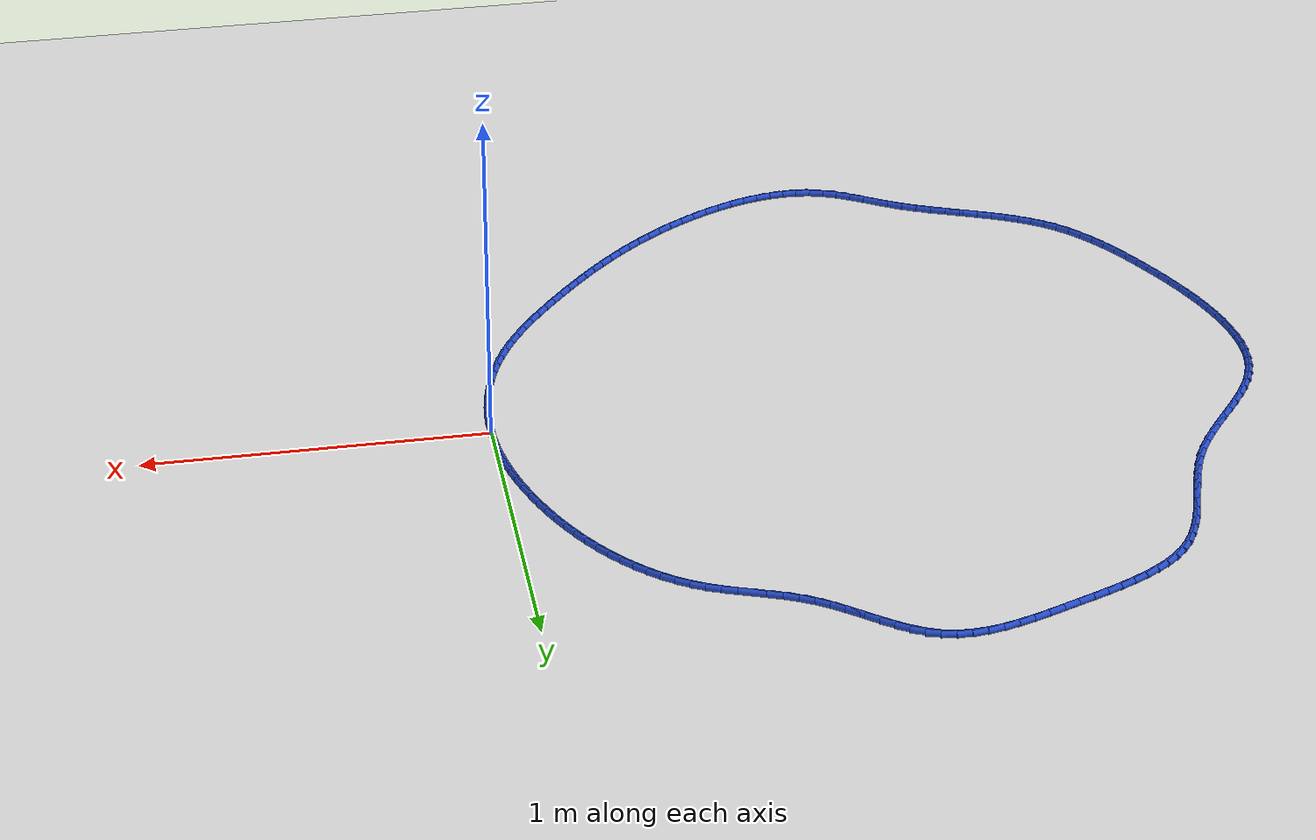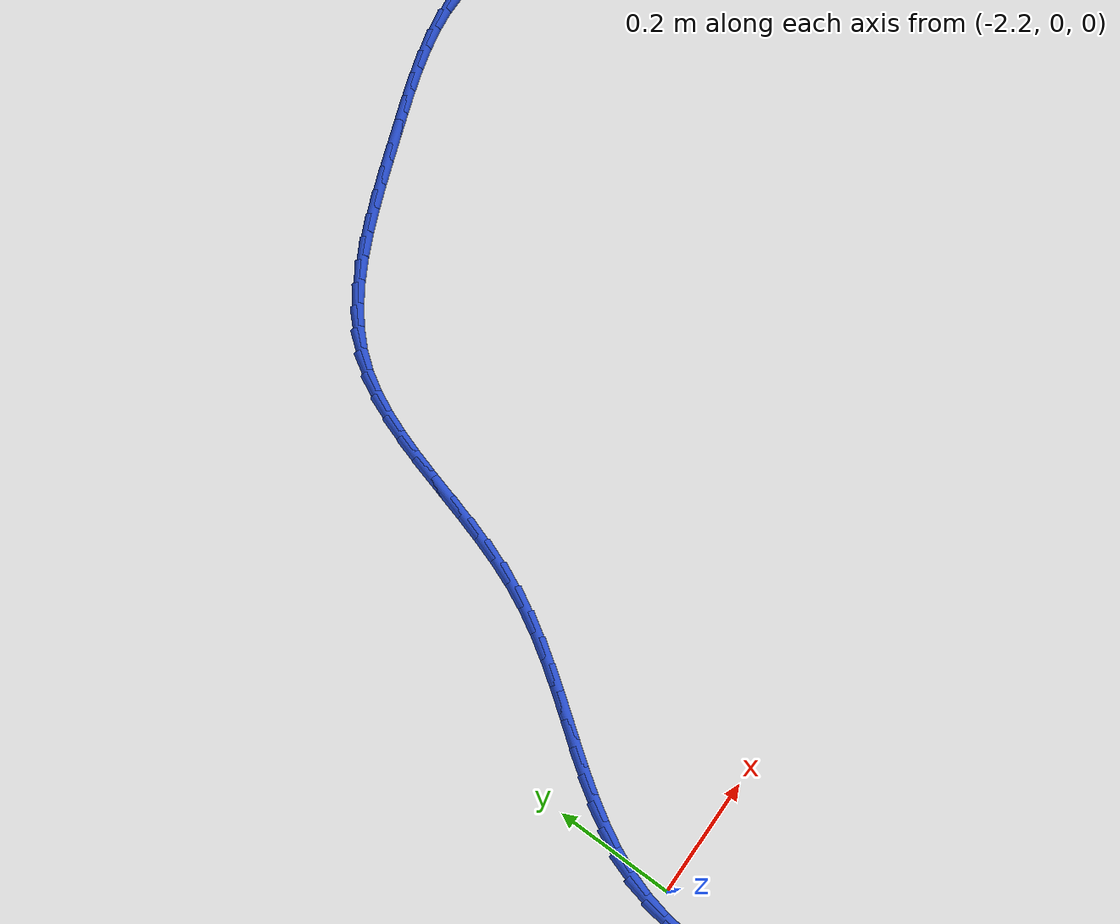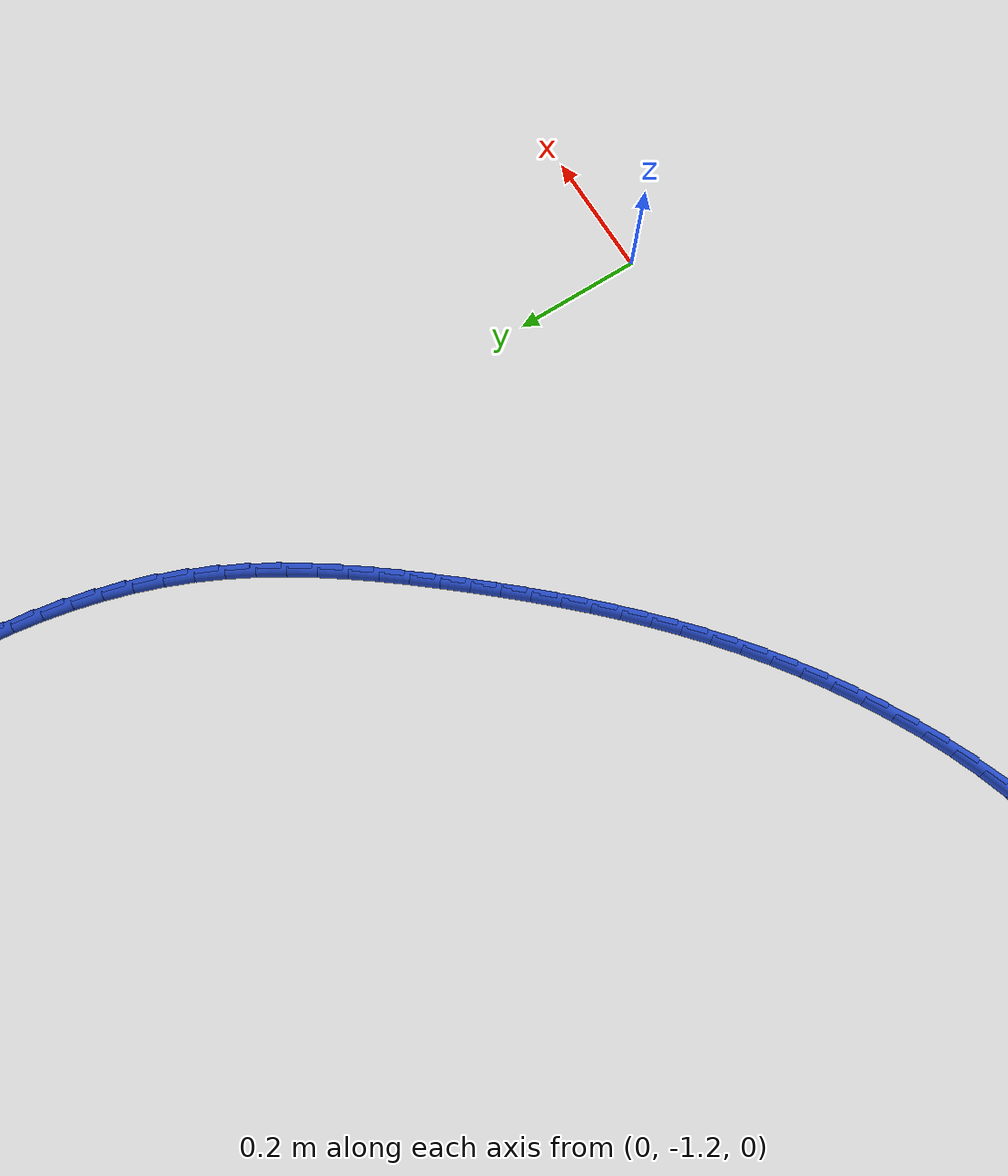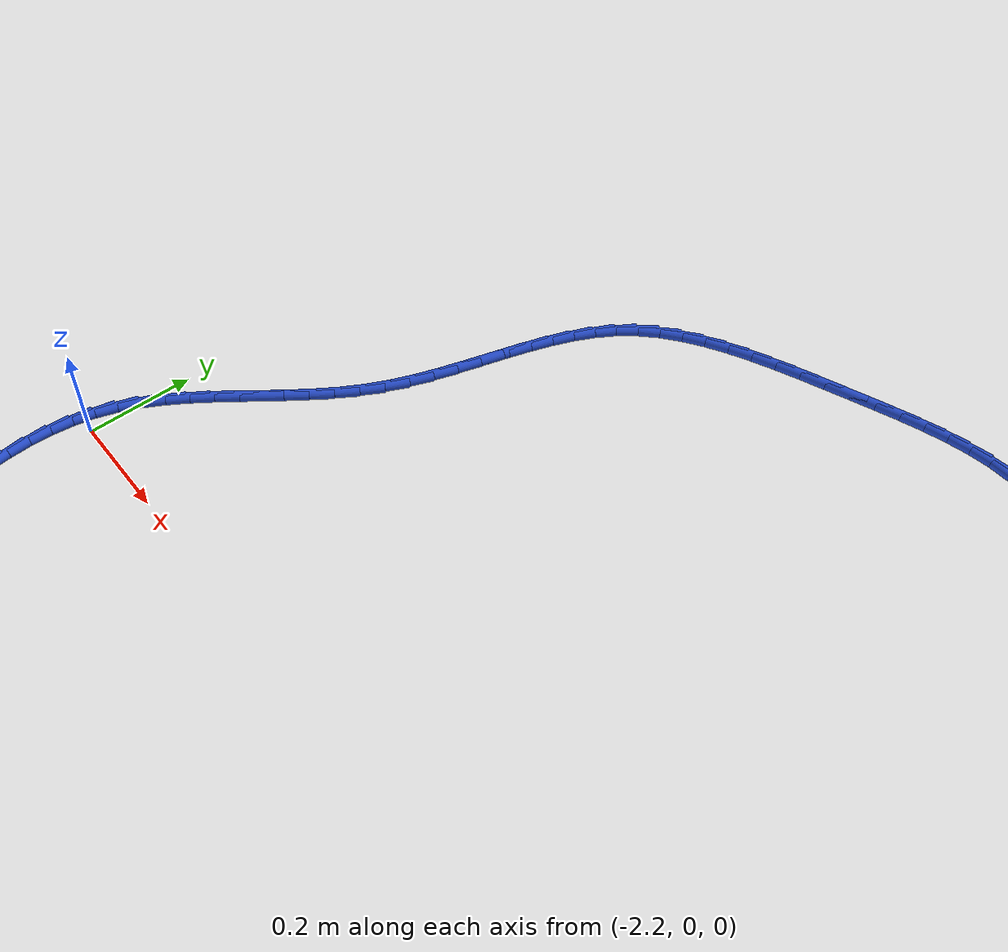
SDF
<sdf version="1.6">
 <world name="default">
  <light name="sun" type="directional">
   <pose>0 0 10 0 -0 0</pose>
   <diffuse>0.8 0.8 0.8 1</diffuse>
   <specular>0.2 0.2 0.2 1</specular>
   <attenuation>
    <range>1000</range>
    <constant>0.9</constant>
    <linear>0.01</linear>
    <quadratic>0.001</quadratic>
   </attenuation>
   <direction>-0.5 0.1 -0.9</direction>
  </light>
  <model name="ground_plane">
   <static>1</static>
   <link name="link">
    <collision name="collision">
     <geometry><plane><normal>0 0 1</normal><size>100 100</size></plane></geometry>
     <surface><friction><ode><mu>100</mu><mu2>50</mu2></ode></friction></surface>
    </collision>
    <visual name="visual">
     <cast_shadows>0</cast_shadows>
     <geometry><plane><normal>0 0 1</normal><size>100 100</size></plane></geometry>
     <material>
      <script><uri>file://media/materials/scripts/gazebo.material</uri><name>Gazebo/WhiteGlow</name></script>
     </material>
    </visual>
   </link>
  </model>
  <gravity>0 0 -9.8</gravity>
  <magnetic_field>6e-06 2.3e-05 -4.2e-05</magnetic_field>
  <atmosphere type="adiabatic"/>
  <physics name="default_physics" default="0" type="ode">
   <max_step_size>0.001</max_step_size>
   <real_time_factor>1</real_time_factor>
   <real_time_update_rate>1000</real_time_update_rate>
  </physics>
  <scene><ambient>0.4 0.4 0.4 1</ambient><background>0.7 0.7 0.7 1</background><shadows>1</shadows></scene>
  <spherical_coordinates>
   <surface_model>EARTH_WGS84</surface_model>
   <latitude_deg>0</latitude_deg>
   <longitude_deg>0</longitude_deg>
   <elevation>0</elevation>
   <heading_deg>0</heading_deg>
  </spherical_coordinates>
  <model name="line">
   <link name="link_0">
    <pose>-2.2551405187698492e-17 -1.3877787807814457e-17 0.01 0 1.57 -1.5382861405999835</pose>
    <collision name="collision">
     <geometry><cylinder><radius>0.01</radius><length>0.08</length></cylinder></geometry>
    </collision>
    <visual name="visual">
     <material>
      <script><name>Gazebo/Blue</name><uri>file://media/materials/scripts/gazebo.material</uri></script>
     </material>
     <geometry><cylinder><radius>0.01</radius><length>0.08</length></cylinder></geometry>
    </visual>
   </link>
   <link name="link_1">
    <pose>-0.0014334239305435637 0.04407599775907522 0.01 0 1.57 -1.4936702109466664</pose>
    <collision name="collision">
     <geometry><cylinder><radius>0.01</radius><length>0.08</length></cylinder></geometry>
    </collision>
    <visual name="visual">
     <material>
      <script><name>Gazebo/Blue</name><uri>file://media/materials/scripts/gazebo.material</uri></script>
     </material>
     <geometry><cylinder><radius>0.01</radius><length>0.08</length></cylinder></geometry>
    </visual>
   </link>
   <link name="link_2">
    <pose>-0.004822178645681405 0.08792667980544557 0.01 0 1.57 -1.4501386980999926</pose>
    <collision name="collision">
     <geometry><cylinder><radius>0.01</radius><length>0.08</length></cylinder></geometry>
    </collision>
    <visual name="visual">
     <material>
      <script><name>Gazebo/Blue</name><uri>file://media/materials/scripts/gazebo.material</uri></script>
     </material>
     <geometry><cylinder><radius>0.01</radius><length>0.08</length></cylinder></geometry>
    </visual>
   </link>
   <link name="link_3">
    <pose>-0.010113488527586544 0.1315675797254038 0.01 0 1.57 -1.4078883765657173</pose>
    <collision name="collision">
     <geometry><cylinder><radius>0.01</radius><length>0.08</length></cylinder></geometry>
    </collision>
    <visual name="visual">
     <material>
      <script><name>Gazebo/Blue</name><uri>file://media/materials/scripts/gazebo.material</uri></script>
     </material>
     <geometry><cylinder><radius>0.01</radius><length>0.08</length></cylinder></geometry>
    </visual>
   </link>
   <link name="link_4">
    <pose>-0.01725457795843197 0.1750142311052427 0.01 0 1.57 -1.36708628930092</pose>
    <collision name="collision">
     <geometry><cylinder><radius>0.01</radius><length>0.08</length></cylinder></geometry>
    </collision>
    <visual name="visual">
     <material>
      <script><name>Gazebo/Blue</name><uri>file://media/materials/scripts/gazebo.material</uri></script>
     </material>
     <geometry><cylinder><radius>0.01</radius><length>0.08</length></cylinder></geometry>
    </visual>
   </link>
   <link name="link_5">
    <pose>-0.02619267132039068 0.21828216753125507 0.01 0 1.57 -1.3278682648668352</pose>
    <collision name="collision">
     <geometry><cylinder><radius>0.01</radius><length>0.08</length></cylinder></geometry>
    </collision>
    <visual name="visual">
     <material>
      <script><name>Gazebo/Blue</name><uri>file://media/materials/scripts/gazebo.material</uri></script>
     </material>
     <geometry><cylinder><radius>0.01</radius><length>0.08</length></cylinder></geometry>
    </visual>
   </link>
   <link name="link_6">
    <pose>-0.036874992995635694 0.26138692258973373 0.01 0 1.57 -1.2903390067754423</pose>
    <collision name="collision">
     <geometry><cylinder><radius>0.01</radius><length>0.08</length></cylinder></geometry>
    </collision>
    <visual name="visual">
     <material>
      <script><name>Gazebo/Blue</name><uri>file://media/materials/scripts/gazebo.material</uri></script>
     </material>
     <geometry><cylinder><radius>0.01</radius><length>0.08</length></cylinder></geometry>
    </visual>
   </link>
   <link name="link_7">
    <pose>-0.049248767366339964 0.3043440298669714 0.01 0 1.57 -1.2545734930620167</pose>
    <collision name="collision">
     <geometry><cylinder><radius>0.01</radius><length>0.08</length></cylinder></geometry>
    </collision>
    <visual name="visual">
     <material>
      <script><name>Gazebo/Blue</name><uri>file://media/materials/scripts/gazebo.material</uri></script>
     </material>
     <geometry><cylinder><radius>0.01</radius><length>0.08</length></cylinder></geometry>
    </visual>
   </link>
   <link name="link_8">
    <pose>-0.0632612188146765 0.34716902294926083 0.01 0 1.57 -1.220617000989838</pose>
    <collision name="collision">
     <geometry><cylinder><radius>0.01</radius><length>0.08</length></cylinder></geometry>
    </collision>
    <visual name="visual">
     <material>
      <script><name>Gazebo/Blue</name><uri>file://media/materials/scripts/gazebo.material</uri></script>
     </material>
     <geometry><cylinder><radius>0.01</radius><length>0.08</length></cylinder></geometry>
    </visual>
   </link>
   <link name="link_9">
    <pose>-0.07885961957642132 0.38987725323400174 0.01 0 1.57 -1.187687017059965</pose>
    <collision name="collision">
     <geometry><cylinder><radius>0.01</radius><length>0.08</length></cylinder></geometry>
    </collision>
    <visual name="visual">
     <material>
      <script><name>Gazebo/Blue</name><uri>file://media/materials/scripts/gazebo.material</uri></script>
     </material>
     <geometry><cylinder><radius>0.01</radius><length>0.08</length></cylinder></geometry>
    </visual>
   </link>
   <link name="link_10">
    <pose>-0.09600698006412178 0.43242415351632935 0.01 0 1.57 -1.1536730512228142</pose>
    <collision name="collision">
     <geometry><cylinder><radius>0.01</radius><length>0.08</length></cylinder></geometry>
    </collision>
    <visual name="visual">
     <material>
      <script><name>Gazebo/Blue</name><uri>file://media/materials/scripts/gazebo.material</uri></script>
     </material>
     <geometry><cylinder><radius>0.01</radius><length>0.08</length></cylinder></geometry>
    </visual>
   </link>
   <link name="link_11">
    <pose>-0.11470467641745499 0.47461909006932423 0.01 0 1.57 -1.1179699331308197</pose>
    <collision name="collision">
     <geometry><cylinder><radius>0.01</radius><length>0.08</length></cylinder></geometry>
    </collision>
    <visual name="visual">
     <material>
      <script><name>Gazebo/Blue</name><uri>file://media/materials/scripts/gazebo.material</uri></script>
     </material>
     <geometry><cylinder><radius>0.01</radius><length>0.08</length></cylinder></geometry>
    </visual>
   </link>
   <link name="link_12">
    <pose>-0.13495982042169669 0.5162495923375483 0.01 0 1.57 -1.080246169833982</pose>
    <collision name="collision">
     <geometry><cylinder><radius>0.01</radius><length>0.08</length></cylinder></geometry>
    </collision>
    <visual name="visual">
     <material>
      <script><name>Gazebo/Blue</name><uri>file://media/materials/scripts/gazebo.material</uri></script>
     </material>
     <geometry><cylinder><radius>0.01</radius><length>0.08</length></cylinder></geometry>
    </visual>
   </link>
   <link name="link_13">
    <pose>-0.15677952386212246 0.5571031897655633 0.01 0 1.57 -1.040156994830927</pose>
    <collision name="collision">
     <geometry><cylinder><radius>0.01</radius><length>0.08</length></cylinder></geometry>
    </collision>
    <visual name="visual">
     <material>
      <script><name>Gazebo/Blue</name><uri>file://media/materials/scripts/gazebo.material</uri></script>
     </material>
     <geometry><cylinder><radius>0.01</radius><length>0.08</length></cylinder></geometry>
    </visual>
   </link>
   <link name="link_14">
    <pose>-0.18017089852400817 0.5969674117979313 0.01 0 1.57 -0.9973429066233543</pose>
    <collision name="collision">
     <geometry><cylinder><radius>0.01</radius><length>0.08</length></cylinder></geometry>
    </collision>
    <visual name="visual">
     <material>
      <script><name>Gazebo/Blue</name><uri>file://media/materials/scripts/gazebo.material</uri></script>
     </material>
     <geometry><cylinder><radius>0.01</radius><length>0.08</length></cylinder></geometry>
    </visual>
   </link>
   <link name="link_15">
    <pose>-0.20514105619262946 0.6356297878792139 0.01 0 1.57 -0.9514309978935486</pose>
    <collision name="collision">
     <geometry><cylinder><radius>0.01</radius><length>0.08</length></cylinder></geometry>
    </collision>
    <visual name="visual">
     <material>
      <script><name>Gazebo/Blue</name><uri>file://media/materials/scripts/gazebo.material</uri></script>
     </material>
     <geometry><cylinder><radius>0.01</radius><length>0.08</length></cylinder></geometry>
    </visual>
   </link>
   <link name="link_16">
    <pose>-0.2316971086532621 0.672877847453973 0.01 0 1.57 -0.9020401060629332</pose>
    <collision name="collision">
     <geometry><cylinder><radius>0.01</radius><length>0.08</length></cylinder></geometry>
    </collision>
    <visual name="visual">
     <material>
      <script><name>Gazebo/Blue</name><uri>file://media/materials/scripts/gazebo.material</uri></script>
     </material>
     <geometry><cylinder><radius>0.01</radius><length>0.08</length></cylinder></geometry>
    </visual>
   </link>
   <link name="link_17">
    <pose>-0.25984616769118185 0.7084991199667707 0.01 0 1.57 -0.8487911784078503</pose>
    <collision name="collision">
     <geometry><cylinder><radius>0.01</radius><length>0.08</length></cylinder></geometry>
    </collision>
    <visual name="visual">
     <material>
      <script><name>Gazebo/Blue</name><uri>file://media/materials/scripts/gazebo.material</uri></script>
     </material>
     <geometry><cylinder><radius>0.01</radius><length>0.08</length></cylinder></geometry>
    </visual>
   </link>
   <link name="link_18">
    <pose>-0.2895953450916642 0.7422811348621686 0.01 0 1.57 -0.7913245287181514</pose>
    <collision name="collision">
     <geometry><cylinder><radius>0.01</radius><length>0.08</length></cylinder></geometry>
    </collision>
    <visual name="visual">
     <material>
      <script><name>Gazebo/Blue</name><uri>file://media/materials/scripts/gazebo.material</uri></script>
     </material>
     <geometry><cylinder><radius>0.01</radius><length>0.08</length></cylinder></geometry>
    </visual>
   </link>
   <link name="link_19">
    <pose>-0.3209517526399851 0.7740114215847285 0.01 0 1.57 -0.7293256935071399</pose>
    <collision name="collision">
     <geometry><cylinder><radius>0.01</radius><length>0.08</length></cylinder></geometry>
    </collision>
    <visual name="visual">
     <material>
      <script><name>Gazebo/Blue</name><uri>file://media/materials/scripts/gazebo.material</uri></script>
     </material>
     <geometry><cylinder><radius>0.01</radius><length>0.08</length></cylinder></geometry>
    </visual>
   </link>
   <link name="link_20">
    <pose>-0.35392250212142035 0.8034775095790125 0.01 0 1.57 -0.6625610832341257</pose>
    <collision name="collision">
     <geometry><cylinder><radius>0.01</radius><length>0.08</length></cylinder></geometry>
    </collision>
    <visual name="visual">
     <material>
      <script><name>Gazebo/Blue</name><uri>file://media/materials/scripts/gazebo.material</uri></script>
     </material>
     <geometry><cylinder><radius>0.01</radius><length>0.08</length></cylinder></geometry>
    </visual>
   </link>
   <link name="link_21">
    <pose>-0.38851470532124543 0.8304669282895821 0.01 0 1.57 -0.5909231779928814</pose>
    <collision name="collision">
     <geometry><cylinder><radius>0.01</radius><length>0.08</length></cylinder></geometry>
    </collision>
    <visual name="visual">
     <material>
      <script><name>Gazebo/Blue</name><uri>file://media/materials/scripts/gazebo.material</uri></script>
     </material>
     <geometry><cylinder><radius>0.01</radius><length>0.08</length></cylinder></geometry>
    </visual>
   </link>
   <link name="link_22">
    <pose>-0.4247354740247361 0.8547672071609995 0.01 0 1.57 -0.5144822797709827</pose>
    <collision name="collision">
     <geometry><cylinder><radius>0.01</radius><length>0.08</length></cylinder></geometry>
    </collision>
    <visual name="visual">
     <material>
      <script><name>Gazebo/Blue</name><uri>file://media/materials/scripts/gazebo.material</uri></script>
     </material>
     <geometry><cylinder><radius>0.01</radius><length>0.08</length></cylinder></geometry>
    </visual>
   </link>
   <link name="link_23">
    <pose>-0.4625919200171682 0.8761658756378263 0.01 0 1.57 -0.4366021855294187</pose>
    <collision name="collision">
     <geometry><cylinder><radius>0.01</radius><length>0.08</length></cylinder></geometry>
    </collision>
    <visual name="visual">
     <material>
      <script><name>Gazebo/Blue</name><uri>file://media/materials/scripts/gazebo.material</uri></script>
     </material>
     <geometry><cylinder><radius>0.01</radius><length>0.08</length></cylinder></geometry>
    </visual>
   </link>
   <link name="link_24">
    <pose>-0.502043563912625 0.8945754429551186 0.01 0 1.57 -0.37847249612537864</pose>
    <collision name="collision">
     <geometry><cylinder><radius>0.01</radius><length>0.08</length></cylinder></geometry>
    </collision>
    <visual name="visual">
     <material>
      <script><name>Gazebo/Blue</name><uri>file://media/materials/scripts/gazebo.material</uri></script>
     </material>
     <geometry><cylinder><radius>0.01</radius><length>0.08</length></cylinder></geometry>
    </visual>
   </link>
   <link name="link_25">
    <pose>-0.5427281735658166 0.910753377432773 0.01 0 1.57 -0.34858247399980025</pose>
    <collision name="collision">
     <geometry><cylinder><radius>0.01</radius><length>0.08</length></cylinder></geometry>
    </collision>
    <visual name="visual">
     <material>
      <script><name>Gazebo/Blue</name><uri>file://media/materials/scripts/gazebo.material</uri></script>
     </material>
     <geometry><cylinder><radius>0.01</radius><length>0.08</length></cylinder></geometry>
    </visual>
   </link>
   <link name="link_26">
    <pose>-0.5841502539382211 0.925807110799015 0.01 0 1.57 -0.34638778234710227</pose>
    <collision name="collision">
     <geometry><cylinder><radius>0.01</radius><length>0.08</length></cylinder></geometry>
    </collision>
    <visual name="visual">
     <material>
      <script><name>Gazebo/Blue</name><uri>file://media/materials/scripts/gazebo.material</uri></script>
     </material>
     <geometry><cylinder><radius>0.01</radius><length>0.08</length></cylinder></geometry>
    </visual>
   </link>
   <link name="link_27">
    <pose>-0.6258138833328433 0.9408451952354079 0.01 0 1.57 -0.37146566927412505</pose>
    <collision name="collision">
     <geometry><cylinder><radius>0.01</radius><length>0.08</length></cylinder></geometry>
    </collision>
    <visual name="visual">
     <material>
      <script><name>Gazebo/Blue</name><uri>file://media/materials/scripts/gazebo.material</uri></script>
     </material>
     <geometry><cylinder><radius>0.01</radius><length>0.08</length></cylinder></geometry>
    </visual>
   </link>
   <link name="link_28">
    <pose>-0.6672231400526876 0.956976182923513 0.01 0 1.57 -0.423588154599452</pose>
    <collision name="collision">
     <geometry><cylinder><radius>0.01</radius><length>0.08</length></cylinder></geometry>
    </collision>
    <visual name="visual">
     <material>
      <script><name>Gazebo/Blue</name><uri>file://media/materials/scripts/gazebo.material</uri></script>
     </material>
     <geometry><cylinder><radius>0.01</radius><length>0.08</length></cylinder></geometry>
    </visual>
   </link>
   <link name="link_29">
    <pose>-0.7078821024007586 0.9753086260448929 0.01 0 1.57 -0.5020561101154503</pose>
    <collision name="collision">
     <geometry><cylinder><radius>0.01</radius><length>0.08</length></cylinder></geometry>
    </collision>
    <visual name="visual">
     <material>
      <script><name>Gazebo/Blue</name><uri>file://media/materials/scripts/gazebo.material</uri></script>
     </material>
     <geometry><cylinder><radius>0.01</radius><length>0.08</length></cylinder></geometry>
    </visual>
   </link>
   <link name="link_30">
    <pose>-0.7472966116673565 0.9969462159104073 0.01 0 1.57 -0.5884187493287651</pose>
    <collision name="collision">
     <geometry><cylinder><radius>0.01</radius><length>0.08</length></cylinder></geometry>
    </collision>
    <visual name="visual">
     <material>
      <script><name>Gazebo/Blue</name><uri>file://media/materials/scripts/gazebo.material</uri></script>
     </material>
     <geometry><cylinder><radius>0.01</radius><length>0.08</length></cylinder></geometry>
    </visual>
   </link>
   <link name="link_31">
    <pose>-0.7852372262880111 1.0222627714040464 0.01 0 1.57 -0.6483921212265681</pose>
    <collision name="collision">
     <geometry><cylinder><radius>0.01</radius><length>0.08</length></cylinder></geometry>
    </collision>
    <visual name="visual">
     <material>
      <script><name>Gazebo/Blue</name><uri>file://media/materials/scripts/gazebo.material</uri></script>
     </material>
     <geometry><cylinder><radius>0.01</radius><length>0.08</length></cylinder></geometry>
    </visual>
   </link>
   <link name="link_32">
    <pose>-0.8220188884349133 1.0501311482640994 0.01 0 1.57 -0.6798790047006336</pose>
    <collision name="collision">
     <geometry><cylinder><radius>0.01</radius><length>0.08</length></cylinder></geometry>
    </collision>
    <visual name="visual">
     <material>
      <script><name>Gazebo/Blue</name><uri>file://media/materials/scripts/gazebo.material</uri></script>
     </material>
     <geometry><cylinder><radius>0.01</radius><length>0.08</length></cylinder></geometry>
    </visual>
   </link>
   <link name="link_33">
    <pose>-0.8580235279992464 1.079239505128904 0.01 0 1.57 -0.6840688452375403</pose>
    <collision name="collision">
     <geometry><cylinder><radius>0.01</radius><length>0.08</length></cylinder></geometry>
    </collision>
    <visual name="visual">
     <material>
      <script><name>Gazebo/Blue</name><uri>file://media/materials/scripts/gazebo.material</uri></script>
     </material>
     <geometry><cylinder><radius>0.01</radius><length>0.08</length></cylinder></geometry>
    </visual>
   </link>
   <link name="link_34">
    <pose>-0.8936330748721933 1.1082760006367984 0.01 0 1.57 -0.6604603087573799</pose>
    <collision name="collision">
     <geometry><cylinder><radius>0.01</radius><length>0.08</length></cylinder></geometry>
    </collision>
    <visual name="visual">
     <material>
      <script><name>Gazebo/Blue</name><uri>file://media/materials/scripts/gazebo.material</uri></script>
     </material>
     <geometry><cylinder><radius>0.01</radius><length>0.08</length></cylinder></geometry>
    </visual>
   </link>
   <link name="link_35">
    <pose>-0.929229458944937 1.1359287934261215 0.01 0 1.57 -0.6066395983441721</pose>
    <collision name="collision">
     <geometry><cylinder><radius>0.01</radius><length>0.08</length></cylinder></geometry>
    </collision>
    <visual name="visual">
     <material>
      <script><name>Gazebo/Blue</name><uri>file://media/materials/scripts/gazebo.material</uri></script>
     </material>
     <geometry><cylinder><radius>0.01</radius><length>0.08</length></cylinder></geometry>
    </visual>
   </link>
   <link name="link_36">
    <pose>-0.9651946101086604 1.160886042135211 0.01 0 1.57 -0.5185171730781961</pose>
    <collision name="collision">
     <geometry><cylinder><radius>0.01</radius><length>0.08</length></cylinder></geometry>
    </collision>
    <visual name="visual">
     <material>
      <script><name>Gazebo/Blue</name><uri>file://media/materials/scripts/gazebo.material</uri></script>
     </material>
     <geometry><cylinder><radius>0.01</radius><length>0.08</length></cylinder></geometry>
    </visual>
   </link>
   <link name="link_37">
    <pose>-1.0019104582545468 1.1818359054024055 0.01 0 1.57 -0.39164510755171444</pose>
    <collision name="collision">
     <geometry><cylinder><radius>0.01</radius><length>0.08</length></cylinder></geometry>
    </collision>
    <visual name="visual">
     <material>
      <script><name>Gazebo/Blue</name><uri>file://media/materials/scripts/gazebo.material</uri></script>
     </material>
     <geometry><cylinder><radius>0.01</radius><length>0.08</length></cylinder></geometry>
    </visual>
   </link>
   <link name="link_38">
    <pose>-1.039758933273779 1.197466541866043 0.01 0 1.57 -0.22868922316305312</pose>
    <collision name="collision">
     <geometry><cylinder><radius>0.01</radius><length>0.08</length></cylinder></geometry>
    </collision>
    <visual name="visual">
     <material>
      <script><name>Gazebo/Blue</name><uri>file://media/materials/scripts/gazebo.material</uri></script>
     </material>
     <geometry><cylinder><radius>0.01</radius><length>0.08</length></cylinder></geometry>
    </visual>
   </link>
   <link name="link_39">
    <pose>-1.0790798790291691 1.2066189303432555 0.01 0 1.57 -0.06929005652740972</pose>
    <collision name="collision">
     <geometry><cylinder><radius>0.01</radius><length>0.08</length></cylinder></geometry>
    </collision>
    <visual name="visual">
     <material>
      <script><name>Gazebo/Blue</name><uri>file://media/materials/scripts/gazebo.material</uri></script>
     </material>
     <geometry><cylinder><radius>0.01</radius><length>0.08</length></cylinder></geometry>
    </visual>
   </link>
   <link name="link_40">
    <pose>-1.1198511443910244 1.20944850344067 0.01 0 1.57 0.0634062857955353</pose>
    <collision name="collision">
     <geometry><cylinder><radius>0.01</radius><length>0.08</length></cylinder></geometry>
    </collision>
    <visual name="visual">
     <material>
      <script><name>Gazebo/Blue</name><uri>file://media/materials/scripts/gazebo.material</uri></script>
     </material>
     <geometry><cylinder><radius>0.01</radius><length>0.08</length></cylinder></geometry>
    </visual>
   </link>
   <link name="link_41">
    <pose>-1.161866000317936 1.2067809216424692 0.01 0 1.57 0.1687330409204674</pose>
    <collision name="collision">
     <geometry><cylinder><radius>0.01</radius><length>0.08</length></cylinder></geometry>
    </collision>
    <visual name="visual">
     <material>
      <script><name>Gazebo/Blue</name><uri>file://media/materials/scripts/gazebo.material</uri></script>
     </material>
     <geometry><cylinder><radius>0.01</radius><length>0.08</length></cylinder></geometry>
    </visual>
   </link>
   <link name="link_42">
    <pose>-1.204916245557059 1.1994471912357938 0.01 0 1.57 0.24925367229525305</pose>
    <collision name="collision">
     <geometry><cylinder><radius>0.01</radius><length>0.08</length></cylinder></geometry>
    </collision>
    <visual name="visual">
     <material>
      <script><name>Gazebo/Blue</name><uri>file://media/materials/scripts/gazebo.material</uri></script>
     </material>
     <geometry><cylinder><radius>0.01</radius><length>0.08</length></cylinder></geometry>
    </visual>
   </link>
   <link name="link_43">
    <pose>-1.2487936788555472 1.1882783185077836 0.01 0 1.57 0.308360027195604</pose>
    <collision name="collision">
     <geometry><cylinder><radius>0.01</radius><length>0.08</length></cylinder></geometry>
    </collision>
    <visual name="visual">
     <material>
      <script><name>Gazebo/Blue</name><uri>file://media/materials/scripts/gazebo.material</uri></script>
     </material>
     <geometry><cylinder><radius>0.01</radius><length>0.08</length></cylinder></geometry>
    </visual>
   </link>
   <link name="link_44">
    <pose>-1.2932900989605567 1.1741053097455787 0.01 0 1.57 0.3490904753763662</pose>
    <collision name="collision">
     <geometry><cylinder><radius>0.01</radius><length>0.08</length></cylinder></geometry>
    </collision>
    <visual name="visual">
     <material>
      <script><name>Gazebo/Blue</name><uri>file://media/materials/scripts/gazebo.material</uri></script>
     </material>
     <geometry><cylinder><radius>0.01</radius><length>0.08</length></cylinder></geometry>
    </visual>
   </link>
   <link name="link_45">
    <pose>-1.3381973046192415 1.1577591712363202 0.01 0 1.57 0.37369124129448106</pose>
    <collision name="collision">
     <geometry><cylinder><radius>0.01</radius><length>0.08</length></cylinder></geometry>
    </collision>
    <visual name="visual">
     <material>
      <script><name>Gazebo/Blue</name><uri>file://media/materials/scripts/gazebo.material</uri></script>
     </material>
     <geometry><cylinder><radius>0.01</radius><length>0.08</length></cylinder></geometry>
    </visual>
   </link>
   <link name="link_46">
    <pose>-1.3833070945787562 1.140070909267147 0.01 0 1.57 0.3835225798848618</pose>
    <collision name="collision">
     <geometry><cylinder><radius>0.01</radius><length>0.08</length></cylinder></geometry>
    </collision>
    <visual name="visual">
     <material>
      <script><name>Gazebo/Blue</name><uri>file://media/materials/scripts/gazebo.material</uri></script>
     </material>
     <geometry><cylinder><radius>0.01</radius><length>0.08</length></cylinder></geometry>
    </visual>
   </link>
   <link name="link_47">
    <pose>-1.4284112250598373 1.1218712558541355 0.01 0 1.57 0.38454559225733187</pose>
    <collision name="collision">
     <geometry><cylinder><radius>0.01</radius><length>0.08</length></cylinder></geometry>
    </collision>
    <visual name="visual">
     <material>
      <script><name>Gazebo/Blue</name><uri>file://media/materials/scripts/gazebo.material</uri></script>
     </material>
     <geometry><cylinder><radius>0.01</radius><length>0.08</length></cylinder></geometry>
    </visual>
   </link>
   <link name="link_48">
    <pose>-1.473259659576068 1.103721403964395 0.01 0 1.57 0.3926086089769305</pose>
    <collision name="collision">
     <geometry><cylinder><radius>0.01</radius><length>0.08</length></cylinder></geometry>
    </collision>
    <visual name="visual">
     <material>
      <script><name>Gazebo/Blue</name><uri>file://media/materials/scripts/gazebo.material</uri></script>
     </material>
     <geometry><cylinder><radius>0.01</radius><length>0.08</length></cylinder></geometry>
    </visual>
   </link>
   <link name="link_49">
    <pose>-1.517482337310516 1.0854084583065229 0.01 0 1.57 0.4109457855170791</pose>
    <collision name="collision">
     <geometry><cylinder><radius>0.01</radius><length>0.08</length></cylinder></geometry>
    </collision>
    <visual name="visual">
     <material>
      <script><name>Gazebo/Blue</name><uri>file://media/materials/scripts/gazebo.material</uri></script>
     </material>
     <geometry><cylinder><radius>0.01</radius><length>0.08</length></cylinder></geometry>
    </visual>
   </link>
   <link name="link_50">
    <pose>-1.5606877842269817 1.0665814205766624 0.01 0 1.57 0.4402944311834379</pose>
    <collision name="collision">
     <geometry><cylinder><radius>0.01</radius><length>0.08</length></cylinder></geometry>
    </collision>
    <visual name="visual">
     <material>
      <script><name>Gazebo/Blue</name><uri>file://media/materials/scripts/gazebo.material</uri></script>
     </material>
     <geometry><cylinder><radius>0.01</radius><length>0.08</length></cylinder></geometry>
    </visual>
   </link>
   <link name="link_51">
    <pose>-1.602484526289267 1.0468892924709565 0.01 0 1.57 0.48168179016255697</pose>
    <collision name="collision">
     <geometry><cylinder><radius>0.01</radius><length>0.08</length></cylinder></geometry>
    </collision>
    <visual name="visual">
     <material>
      <script><name>Gazebo/Blue</name><uri>file://media/materials/scripts/gazebo.material</uri></script>
     </material>
     <geometry><cylinder><radius>0.01</radius><length>0.08</length></cylinder></geometry>
    </visual>
   </link>
   <link name="link_52">
    <pose>-1.6424810894611723 1.0259810756855492 0.01 0 1.57 0.5363711308153888</pose>
    <collision name="collision">
     <geometry><cylinder><radius>0.01</radius><length>0.08</length></cylinder></geometry>
    </collision>
    <visual name="visual">
     <material>
      <script><name>Gazebo/Blue</name><uri>file://media/materials/scripts/gazebo.material</uri></script>
     </material>
     <geometry><cylinder><radius>0.01</radius><length>0.08</length></cylinder></geometry>
    </visual>
   </link>
   <link name="link_53">
    <pose>-1.6802859997064987 1.0035057719165836 0.01 0 1.57 0.6057188650561122</pose>
    <collision name="collision">
     <geometry><cylinder><radius>0.01</radius><length>0.08</length></cylinder></geometry>
    </collision>
    <visual name="visual">
     <material>
      <script><name>Gazebo/Blue</name><uri>file://media/materials/scripts/gazebo.material</uri></script>
     </material>
     <geometry><cylinder><radius>0.01</radius><length>0.08</length></cylinder></geometry>
    </visual>
   </link>
   <link name="link_54">
    <pose>-1.7155077829890462 0.9791123828602034 0.01 0 1.57 0.6908793814490248</pose>
    <collision name="collision">
     <geometry><cylinder><radius>0.01</radius><length>0.08</length></cylinder></geometry>
    </collision>
    <visual name="visual">
     <material>
      <script><name>Gazebo/Blue</name><uri>file://media/materials/scripts/gazebo.material</uri></script>
     </material>
     <geometry><cylinder><radius>0.01</radius><length>0.08</length></cylinder></geometry>
    </visual>
   </link>
   <link name="link_55">
    <pose>-1.7477549652726165 0.952449910212552 0.01 0 1.57 0.7923000830408778</pose>
    <collision name="collision">
     <geometry><cylinder><radius>0.01</radius><length>0.08</length></cylinder></geometry>
    </collision>
    <visual name="visual">
     <material>
      <script><name>Gazebo/Blue</name><uri>file://media/materials/scripts/gazebo.material</uri></script>
     </material>
     <geometry><cylinder><radius>0.01</radius><length>0.08</length></cylinder></geometry>
    </visual>
   </link>
   <link name="link_56">
    <pose>-1.776636072521011 0.9231673556697729 0.01 0 1.57 0.9087690044911634</pose>
    <collision name="collision">
     <geometry><cylinder><radius>0.01</radius><length>0.08</length></cylinder></geometry>
    </collision>
    <visual name="visual">
     <material>
      <script><name>Gazebo/Blue</name><uri>file://media/materials/scripts/gazebo.material</uri></script>
     </material>
     <geometry><cylinder><radius>0.01</radius><length>0.08</length></cylinder></geometry>
    </visual>
   </link>
   <link name="link_57">
    <pose>-1.8017681675880184 0.8909201994930536 0.01 0 1.57 1.0248843198372757</pose>
    <collision name="collision">
     <geometry><cylinder><radius>0.01</radius><length>0.08</length></cylinder></geometry>
    </collision>
    <visual name="visual">
     <material>
      <script><name>Gazebo/Blue</name><uri>file://media/materials/scripts/gazebo.material</uri></script>
     </material>
     <geometry><cylinder><radius>0.01</radius><length>0.08</length></cylinder></geometry>
    </visual>
   </link>
   <link name="link_58">
    <pose>-1.823179053414944 0.8556756287099347 0.01 0 1.57 1.120215197360469</pose>
    <collision name="collision">
     <geometry><cylinder><radius>0.01</radius><length>0.08</length></cylinder></geometry>
    </collision>
    <visual name="visual">
     <material>
      <script><name>Gazebo/Blue</name><uri>file://media/materials/scripts/gazebo.material</uri></script>
     </material>
     <geometry><cylinder><radius>0.01</radius><length>0.08</length></cylinder></geometry>
    </visual>
   </link>
   <link name="link_59">
    <pose>-1.841480819856811 0.817844240158773 0.01 0 1.57 1.1933163553659605</pose>
    <collision name="collision">
     <geometry><cylinder><radius>0.01</radius><length>0.08</length></cylinder></geometry>
    </collision>
    <visual name="visual">
     <material>
      <script><name>Gazebo/Blue</name><uri>file://media/materials/scripts/gazebo.material</uri></script>
     </material>
     <geometry><cylinder><radius>0.01</radius><length>0.08</length></cylinder></geometry>
    </visual>
   </link>
   <link name="link_60">
    <pose>-1.8573301601565337 0.7778704797669933 0.01 0 1.57 1.2455285611351712</pose>
    <collision name="collision">
     <geometry><cylinder><radius>0.01</radius><length>0.08</length></cylinder></geometry>
    </collision>
    <visual name="visual">
     <material>
      <script><name>Gazebo/Blue</name><uri>file://media/materials/scripts/gazebo.material</uri></script>
     </material>
     <geometry><cylinder><radius>0.01</radius><length>0.08</length></cylinder></geometry>
    </visual>
   </link>
   <link name="link_61">
    <pose>-1.871383767557026 0.7361987934620216 0.01 0 1.57 1.2785485448006981</pose>
    <collision name="collision">
     <geometry><cylinder><radius>0.01</radius><length>0.08</length></cylinder></geometry>
    </collision>
    <visual name="visual">
     <material>
      <script><name>Gazebo/Blue</name><uri>file://media/materials/scripts/gazebo.material</uri></script>
     </material>
     <geometry><cylinder><radius>0.01</radius><length>0.08</length></cylinder></geometry>
    </visual>
   </link>
   <link name="link_62">
    <pose>-1.8842983353011993 0.6932736271712837 0.01 0 1.57 1.2938345710350279</pose>
    <collision name="collision">
     <geometry><cylinder><radius>0.01</radius><length>0.08</length></cylinder></geometry>
    </collision>
    <visual name="visual">
     <material>
      <script><name>Gazebo/Blue</name><uri>file://media/materials/scripts/gazebo.material</uri></script>
     </material>
     <geometry><cylinder><radius>0.01</radius><length>0.08</length></cylinder></geometry>
    </visual>
   </link>
   <link name="link_63">
    <pose>-1.8967305566319665 0.6495394268222051 0.01 0 1.57 1.2923517157480142</pose>
    <collision name="collision">
     <geometry><cylinder><radius>0.01</radius><length>0.08</length></cylinder></geometry>
    </collision>
    <visual name="visual">
     <material>
      <script><name>Gazebo/Blue</name><uri>file://media/materials/scripts/gazebo.material</uri></script>
     </material>
     <geometry><cylinder><radius>0.01</radius><length>0.08</length></cylinder></geometry>
    </visual>
   </link>
   <link name="link_64">
    <pose>-1.9093371247922413 0.605440638342212 0.01 0 1.57 1.274512764415474</pose>
    <collision name="collision">
     <geometry><cylinder><radius>0.01</radius><length>0.08</length></cylinder></geometry>
    </collision>
    <visual name="visual">
     <material>
      <script><name>Gazebo/Blue</name><uri>file://media/materials/scripts/gazebo.material</uri></script>
     </material>
     <geometry><cylinder><radius>0.01</radius><length>0.08</length></cylinder></geometry>
    </visual>
   </link>
   <link name="link_65">
    <pose>-1.9227747330249367 0.5614217076587296 0.01 0 1.57 1.240233645528943</pose>
    <collision name="collision">
     <geometry><cylinder><radius>0.01</radius><length>0.08</length></cylinder></geometry>
    </collision>
    <visual name="visual">
     <material>
      <script><name>Gazebo/Blue</name><uri>file://media/materials/scripts/gazebo.material</uri></script>
     </material>
     <geometry><cylinder><radius>0.01</radius><length>0.08</length></cylinder></geometry>
    </visual>
   </link>
   <link name="link_66">
    <pose>-1.9377000745729642 0.517927080699183 0.01 0 1.57 1.1890860469862086</pose>
    <collision name="collision">
     <geometry><cylinder><radius>0.01</radius><length>0.08</length></cylinder></geometry>
    </collision>
    <visual name="visual">
     <material>
      <script><name>Gazebo/Blue</name><uri>file://media/materials/scripts/gazebo.material</uri></script>
     </material>
     <geometry><cylinder><radius>0.01</radius><length>0.08</length></cylinder></geometry>
    </visual>
   </link>
   <link name="link_67">
    <pose>-1.9547698426792381 0.4754012033909992 0.01 0 1.57 1.1211913021205593</pose>
    <collision name="collision">
     <geometry><cylinder><radius>0.01</radius><length>0.08</length></cylinder></geometry>
    </collision>
    <visual name="visual">
     <material>
      <script><name>Gazebo/Blue</name><uri>file://media/materials/scripts/gazebo.material</uri></script>
     </material>
     <geometry><cylinder><radius>0.01</radius><length>0.08</length></cylinder></geometry>
    </visual>
   </link>
   <link name="link_68">
    <pose>-1.9746158670658112 0.43427534420811903 0.01 0 1.57 1.0520046978865423</pose>
    <collision name="collision">
     <geometry><cylinder><radius>0.01</radius><length>0.08</length></cylinder></geometry>
    </collision>
    <visual name="visual">
     <material>
      <script><name>Gazebo/Blue</name><uri>file://media/materials/scripts/gazebo.material</uri></script>
     </material>
     <geometry><cylinder><radius>0.01</radius><length>0.08</length></cylinder></geometry>
    </visual>
   </link>
   <link name="link_69">
    <pose>-1.9972415873577416 0.3946477302455275 0.01 0 1.57 0.9981070855573929</pose>
    <collision name="collision">
     <geometry><cylinder><radius>0.01</radius><length>0.08</length></cylinder></geometry>
    </collision>
    <visual name="visual">
     <material>
      <script><name>Gazebo/Blue</name><uri>file://media/materials/scripts/gazebo.material</uri></script>
     </material>
     <geometry><cylinder><radius>0.01</radius><length>0.08</length></cylinder></geometry>
    </visual>
   </link>
   <link name="link_70">
    <pose>-2.0219889448808264 0.35626600015510995 0.01 0 1.57 0.9601418257347493</pose>
    <collision name="collision">
     <geometry><cylinder><radius>0.01</radius><length>0.08</length></cylinder></geometry>
    </collision>
    <visual name="visual">
     <material>
      <script><name>Gazebo/Blue</name><uri>file://media/materials/scripts/gazebo.material</uri></script>
     </material>
     <geometry><cylinder><radius>0.01</radius><length>0.08</length></cylinder></geometry>
    </visual>
   </link>
   <link name="link_71">
    <pose>-2.048168390326459 0.318861102821748 0.01 0 1.57 0.9378567422525881</pose>
    <collision name="collision">
     <geometry><cylinder><radius>0.01</radius><length>0.08</length></cylinder></geometry>
    </collision>
    <visual name="visual">
     <material>
      <script><name>Gazebo/Blue</name><uri>file://media/materials/scripts/gazebo.material</uri></script>
     </material>
     <geometry><cylinder><radius>0.01</radius><length>0.08</length></cylinder></geometry>
    </visual>
   </link>
   <link name="link_72">
    <pose>-2.0750903743860336 0.28216398713032415 0.01 0 1.57 0.931168751454211</pose>
    <collision name="collision">
     <geometry><cylinder><radius>0.01</radius><length>0.08</length></cylinder></geometry>
    </collision>
    <visual name="visual">
     <material>
      <script><name>Gazebo/Blue</name><uri>file://media/materials/scripts/gazebo.material</uri></script>
     </material>
     <geometry><cylinder><radius>0.01</radius><length>0.08</length></cylinder></geometry>
    </visual>
   </link>
   <link name="link_73">
    <pose>-2.102065347750941 0.24590560196572 0.01 0 1.57 0.9403332175462684</pose>
    <collision name="collision">
     <geometry><cylinder><radius>0.01</radius><length>0.08</length></cylinder></geometry>
    </collision>
    <visual name="visual">
     <material>
      <script><name>Gazebo/Blue</name><uri>file://media/materials/scripts/gazebo.material</uri></script>
     </material>
     <geometry><cylinder><radius>0.01</radius><length>0.08</length></cylinder></geometry>
    </visual>
   </link>
   <link name="link_74">
    <pose>-2.1284037611125752 0.20981689621281807 0.01 0 1.57 0.9660175893733108</pose>
    <collision name="collision">
     <geometry><cylinder><radius>0.01</radius><length>0.08</length></cylinder></geometry>
    </collision>
    <visual name="visual">
     <material>
      <script><name>Gazebo/Blue</name><uri>file://media/materials/scripts/gazebo.material</uri></script>
     </material>
     <geometry><cylinder><radius>0.01</radius><length>0.08</length></cylinder></geometry>
    </visual>
   </link>
   <link name="link_75">
    <pose>-2.153416065162331 0.1736288187565002 0.01 0 1.57 1.0092746851901062</pose>
    <collision name="collision">
     <geometry><cylinder><radius>0.01</radius><length>0.08</length></cylinder></geometry>
    </collision>
    <visual name="visual">
     <material>
      <script><name>Gazebo/Blue</name><uri>file://media/materials/scripts/gazebo.material</uri></script>
     </material>
     <geometry><cylinder><radius>0.01</radius><length>0.08</length></cylinder></geometry>
    </visual>
   </link>
   <link name="link_76">
    <pose>-2.176412710591599 0.1370723184816479 0.01 0 1.57 1.0713705532278606</pose>
    <collision name="collision">
     <geometry><cylinder><radius>0.01</radius><length>0.08</length></cylinder></geometry>
    </collision>
    <visual name="visual">
     <material>
      <script><name>Gazebo/Blue</name><uri>file://media/materials/scripts/gazebo.material</uri></script>
     </material>
     <geometry><cylinder><radius>0.01</radius><length>0.08</length></cylinder></geometry>
    </visual>
   </link>
   <link name="link_77">
    <pose>-2.196704148091773 0.09987834427314392 0.01 0 1.57 1.1533804788174757</pose>
    <collision name="collision">
     <geometry><cylinder><radius>0.01</radius><length>0.08</length></cylinder></geometry>
    </collision>
    <visual name="visual">
     <material>
      <script><name>Gazebo/Blue</name><uri>file://media/materials/scripts/gazebo.material</uri></script>
     </material>
     <geometry><cylinder><radius>0.01</radius><length>0.08</length></cylinder></geometry>
    </visual>
   </link>
   <link name="link_78">
    <pose>-2.2136008283542474 0.061777845015869706 0.01 0 1.57 1.254398000918911</pose>
    <collision name="collision">
     <geometry><cylinder><radius>0.01</radius><length>0.08</length></cylinder></geometry>
    </collision>
    <visual name="visual">
     <material>
      <script><name>Gazebo/Blue</name><uri>file://media/materials/scripts/gazebo.material</uri></script>
     </material>
     <geometry><cylinder><radius>0.01</radius><length>0.08</length></cylinder></geometry>
    </visual>
   </link>
   <link name="link_79">
    <pose>-2.226453846337014 0.02251963537410324 0.01 0 1.57 1.3591356717932284</pose>
    <collision name="collision">
     <geometry><cylinder><radius>0.01</radius><length>0.08</length></cylinder></geometry>
    </collision>
    <visual name="visual">
     <material>
      <script><name>Gazebo/Blue</name><uri>file://media/materials/scripts/gazebo.material</uri></script>
     </material>
     <geometry><cylinder><radius>0.01</radius><length>0.08</length></cylinder></geometry>
    </visual>
   </link>
   <link name="link_80">
    <pose>-2.2351424718844726 -0.01791530302333704 0.01 0 1.57 1.456207721410758</pose>
    <collision name="collision">
     <geometry><cylinder><radius>0.01</radius><length>0.08</length></cylinder></geometry>
    </collision>
    <visual name="visual">
     <material>
      <script><name>Gazebo/Blue</name><uri>file://media/materials/scripts/gazebo.material</uri></script>
     </material>
     <geometry><cylinder><radius>0.01</radius><length>0.08</length></cylinder></geometry>
    </visual>
   </link>
   <link name="link_81">
    <pose>-2.2399151850533783 -0.059383696820994744 0.01 0 1.57 1.5445282037850865</pose>
    <collision name="collision">
     <geometry><cylinder><radius>0.01</radius><length>0.08</length></cylinder></geometry>
    </collision>
    <visual name="visual">
     <material>
      <script><name>Gazebo/Blue</name><uri>file://media/materials/scripts/gazebo.material</uri></script>
     </material>
     <geometry><cylinder><radius>0.01</radius><length>0.08</length></cylinder></geometry>
    </visual>
   </link>
   <link name="link_82">
    <pose>-2.2410280339220083 -0.10173894602932239 0.01 0 1.57 -1.5176860795600424</pose>
    <collision name="collision">
     <geometry><cylinder><radius>0.01</radius><length>0.08</length></cylinder></geometry>
    </collision>
    <visual name="visual">
     <material>
      <script><name>Gazebo/Blue</name><uri>file://media/materials/scripts/gazebo.material</uri></script>
     </material>
     <geometry><cylinder><radius>0.01</radius><length>0.08</length></cylinder></geometry>
    </visual>
   </link>
   <link name="link_83">
    <pose>-2.2387370665686386 -0.14483445065876996 0.01 0 1.57 -1.446946403528091</pose>
    <collision name="collision">
     <geometry><cylinder><radius>0.01</radius><length>0.08</length></cylinder></geometry>
    </collision>
    <visual name="visual">
     <material>
      <script><name>Gazebo/Blue</name><uri>file://media/materials/scripts/gazebo.material</uri></script>
     </material>
     <geometry><cylinder><radius>0.01</radius><length>0.08</length></cylinder></geometry>
    </visual>
   </link>
   <link name="link_84">
    <pose>-2.233298331071546 -0.18852361071978993 0.01 0 1.57 -1.384246684867755</pose>
    <collision name="collision">
     <geometry><cylinder><radius>0.01</radius><length>0.08</length></cylinder></geometry>
    </collision>
    <visual name="visual">
     <material>
      <script><name>Gazebo/Blue</name><uri>file://media/materials/scripts/gazebo.material</uri></script>
     </material>
     <geometry><cylinder><radius>0.01</radius><length>0.08</length></cylinder></geometry>
    </visual>
   </link>
   <link name="link_85">
    <pose>-2.2249678755090057 -0.23265982622283388 0.01 0 1.57 -1.328849567010096</pose>
    <collision name="collision">
     <geometry><cylinder><radius>0.01</radius><length>0.08</length></cylinder></geometry>
    </collision>
    <visual name="visual">
     <material>
      <script><name>Gazebo/Blue</name><uri>file://media/materials/scripts/gazebo.material</uri></script>
     </material>
     <geometry><cylinder><radius>0.01</radius><length>0.08</length></cylinder></geometry>
    </visual>
   </link>
   <link name="link_86">
    <pose>-2.214001747959294 -0.27709649717835333 0.01 0 1.57 -1.279985832267244</pose>
    <collision name="collision">
     <geometry><cylinder><radius>0.01</radius><length>0.08</length></cylinder></geometry>
    </collision>
    <visual name="visual">
     <material>
      <script><name>Gazebo/Blue</name><uri>file://media/materials/scripts/gazebo.material</uri></script>
     </material>
     <geometry><cylinder><radius>0.01</radius><length>0.08</length></cylinder></geometry>
    </visual>
   </link>
   <link name="link_87">
    <pose>-2.200655996500688 -0.32168702359680096 0.01 0 1.57 -1.2369187536315462</pose>
    <collision name="collision">
     <geometry><cylinder><radius>0.01</radius><length>0.08</length></cylinder></geometry>
    </collision>
    <visual name="visual">
     <material>
      <script><name>Gazebo/Blue</name><uri>file://media/materials/scripts/gazebo.material</uri></script>
     </material>
     <geometry><cylinder><radius>0.01</radius><length>0.08</length></cylinder></geometry>
    </visual>
   </link>
   <link name="link_88">
    <pose>-2.1851866692114625 -0.3662848054886264 0.01 0 1.57 -1.1989780417414144</pose>
    <collision name="collision">
     <geometry><cylinder><radius>0.01</radius><length>0.08</length></cylinder></geometry>
    </collision>
    <visual name="visual">
     <material>
      <script><name>Gazebo/Blue</name><uri>file://media/materials/scripts/gazebo.material</uri></script>
     </material>
     <geometry><cylinder><radius>0.01</radius><length>0.08</length></cylinder></geometry>
    </visual>
   </link>
   <link name="link_89">
    <pose>-2.1678498141698945 -0.41074324286428243 0.01 0 1.57 -1.1655743572428217</pose>
    <collision name="collision">
     <geometry><cylinder><radius>0.01</radius><length>0.08</length></cylinder></geometry>
    </collision>
    <visual name="visual">
     <material>
      <script><name>Gazebo/Blue</name><uri>file://media/materials/scripts/gazebo.material</uri></script>
     </material>
     <geometry><cylinder><radius>0.01</radius><length>0.08</length></cylinder></geometry>
    </visual>
   </link>
   <link name="link_90">
    <pose>-2.1489014794542607 -0.4549157357342206 0.01 0 1.57 -1.136202604313997</pose>
    <collision name="collision">
     <geometry><cylinder><radius>0.01</radius><length>0.08</length></cylinder></geometry>
    </collision>
    <visual name="visual">
     <material>
      <script><name>Gazebo/Blue</name><uri>file://media/materials/scripts/gazebo.material</uri></script>
     </material>
     <geometry><cylinder><radius>0.01</radius><length>0.08</length></cylinder></geometry>
    </visual>
   </link>
   <link name="link_91">
    <pose>-2.128597713142836 -0.4986556841088924 0.01 0 1.57 -1.1104395393298883</pose>
    <collision name="collision">
     <geometry><cylinder><radius>0.01</radius><length>0.08</length></cylinder></geometry>
    </collision>
    <visual name="visual">
     <material>
      <script><name>Gazebo/Blue</name><uri>file://media/materials/scripts/gazebo.material</uri></script>
     </material>
     <geometry><cylinder><radius>0.01</radius><length>0.08</length></cylinder></geometry>
    </visual>
   </link>
   <link name="link_92">
    <pose>-2.107194563313897 -0.5418164879987502 0.01 0 1.57 -1.0879392030309556</pose>
    <collision name="collision">
     <geometry><cylinder><radius>0.01</radius><length>0.08</length></cylinder></geometry>
    </collision>
    <visual name="visual">
     <material>
      <script><name>Gazebo/Blue</name><uri>file://media/materials/scripts/gazebo.material</uri></script>
     </material>
     <geometry><cylinder><radius>0.01</radius><length>0.08</length></cylinder></geometry>
    </visual>
   </link>
   <link name="link_93">
    <pose>-2.084948078045721 -0.5842515474142442 0.01 0 1.57 -1.0682261151151187</pose>
    <collision name="collision">
     <geometry><cylinder><radius>0.01</radius><length>0.08</length></cylinder></geometry>
    </collision>
    <visual name="visual">
     <material>
      <script><name>Gazebo/Blue</name><uri>file://media/materials/scripts/gazebo.material</uri></script>
     </material>
     <geometry><cylinder><radius>0.01</radius><length>0.08</length></cylinder></geometry>
    </visual>
   </link>
   <link name="link_94">
    <pose>-2.062104466672744 -0.6258122517291025 0.01 0 1.57 -1.0464372898030727</pose>
    <collision name="collision">
     <geometry><cylinder><radius>0.01</radius><length>0.08</length></cylinder></geometry>
    </collision>
    <visual name="visual">
     <material>
      <script><name>Gazebo/Blue</name><uri>file://media/materials/scripts/gazebo.material</uri></script>
     </material>
     <geometry><cylinder><radius>0.01</radius><length>0.08</length></cylinder></geometry>
    </visual>
   </link>
   <link name="link_95">
    <pose>-2.03868541884764 -0.6663041076795021 0.01 0 1.57 -1.017591166908187</pose>
    <collision name="collision">
     <geometry><cylinder><radius>0.01</radius><length>0.08</length></cylinder></geometry>
    </collision>
    <visual name="visual">
     <material>
      <script><name>Gazebo/Blue</name><uri>file://media/materials/scripts/gazebo.material</uri></script>
     </material>
     <geometry><cylinder><radius>0.01</radius><length>0.08</length></cylinder></geometry>
    </visual>
   </link>
   <link name="link_96">
    <pose>-2.014489084279789 -0.7054869395825318 0.01 0 1.57 -0.9810051014647585</pose>
    <collision name="collision">
     <geometry><cylinder><radius>0.01</radius><length>0.08</length></cylinder></geometry>
    </collision>
    <visual name="visual">
     <material>
      <script><name>Gazebo/Blue</name><uri>file://media/materials/scripts/gazebo.material</uri></script>
     </material>
     <geometry><cylinder><radius>0.01</radius><length>0.08</length></cylinder></geometry>
    </visual>
   </link>
   <link name="link_97">
    <pose>-1.9893039698835977 -0.7431186011624855 0.01 0 1.57 -0.9361642037639525</pose>
    <collision name="collision">
     <geometry><cylinder><radius>0.01</radius><length>0.08</length></cylinder></geometry>
    </collision>
    <visual name="visual">
     <material>
      <script><name>Gazebo/Blue</name><uri>file://media/materials/scripts/gazebo.material</uri></script>
     </material>
     <geometry><cylinder><radius>0.01</radius><length>0.08</length></cylinder></geometry>
    </visual>
   </link>
   <link name="link_98">
    <pose>-1.962918582573478 -0.7789569461436603 0.01 0 1.57 -0.88258654387111</pose>
    <collision name="collision">
     <geometry><cylinder><radius>0.01</radius><length>0.08</length></cylinder></geometry>
    </collision>
    <visual name="visual">
     <material>
      <script><name>Gazebo/Blue</name><uri>file://media/materials/scripts/gazebo.material</uri></script>
     </material>
     <geometry><cylinder><radius>0.01</radius><length>0.08</length></cylinder></geometry>
    </visual>
   </link>
   <link name="link_99">
    <pose>-1.9351214292638383 -0.8127598282503516 0.01 0 1.57 -0.8199211040909373</pose>
    <collision name="collision">
     <geometry><cylinder><radius>0.01</radius><length>0.08</length></cylinder></geometry>
    </collision>
    <visual name="visual">
     <material>
      <script><name>Gazebo/Blue</name><uri>file://media/materials/scripts/gazebo.material</uri></script>
     </material>
     <geometry><cylinder><radius>0.01</radius><length>0.08</length></cylinder></geometry>
    </visual>
   </link>
   <link name="link_100">
    <pose>-1.9057010168690869 -0.8442851012068552 0.01 0 1.57 -0.748083570542131</pose>
    <collision name="collision">
     <geometry><cylinder><radius>0.01</radius><length>0.08</length></cylinder></geometry>
    </collision>
    <visual name="visual">
     <material>
      <script><name>Gazebo/Blue</name><uri>file://media/materials/scripts/gazebo.material</uri></script>
     </material>
     <geometry><cylinder><radius>0.01</radius><length>0.08</length></cylinder></geometry>
    </visual>
   </link>
   <link name="link_101">
    <pose>-1.8744458523036334 -0.8732906187374672 0.01 0 1.57 -0.667428019718976</pose>
    <collision name="collision">
     <geometry><cylinder><radius>0.01</radius><length>0.08</length></cylinder></geometry>
    </collision>
    <visual name="visual">
     <material>
      <script><name>Gazebo/Blue</name><uri>file://media/materials/scripts/gazebo.material</uri></script>
     </material>
     <geometry><cylinder><radius>0.01</radius><length>0.08</length></cylinder></geometry>
    </visual>
   </link>
   <link name="link_102">
    <pose>-1.841144643778166 -0.8995345136663795 0.01 0 1.57 -0.5839360243365451</pose>
    <collision name="collision">
     <geometry><cylinder><radius>0.01</radius><length>0.08</length></cylinder></geometry>
    </collision>
    <visual name="visual">
     <material>
      <script><name>Gazebo/Blue</name><uri>file://media/materials/scripts/gazebo.material</uri></script>
     </material>
     <geometry><cylinder><radius>0.01</radius><length>0.08</length></cylinder></geometry>
    </visual>
   </link>
   <link name="link_103">
    <pose>-1.8057116223277814 -0.9229489578394127 0.01 0 1.57 -0.5124012518794243</pose>
    <collision name="collision">
     <geometry><cylinder><radius>0.01</radius><length>0.08</length></cylinder></geometry>
    </collision>
    <visual name="visual">
     <material>
      <script><name>Gazebo/Blue</name><uri>file://media/materials/scripts/gazebo.material</uri></script>
     </material>
     <geometry><cylinder><radius>0.01</radius><length>0.08</length></cylinder></geometry>
    </visual>
   </link>
   <link name="link_104">
    <pose>-1.7684006156431362 -0.9439369782632712 0.01 0 1.57 -0.45547264716363867</pose>
    <collision name="collision">
     <geometry><cylinder><radius>0.01</radius><length>0.08</length></cylinder></geometry>
    </collision>
    <visual name="visual">
     <material>
      <script><name>Gazebo/Blue</name><uri>file://media/materials/scripts/gazebo.material</uri></script>
     </material>
     <geometry><cylinder><radius>0.01</radius><length>0.08</length></cylinder></geometry>
    </visual>
   </link>
   <link name="link_105">
    <pose>-1.7295223188755482 -0.9629804494153292 0.01 0 1.57 -0.41286586363801</pose>
    <collision name="collision">
     <geometry><cylinder><radius>0.01</radius><length>0.08</length></cylinder></geometry>
    </collision>
    <visual name="visual">
     <material>
      <script><name>Gazebo/Blue</name><uri>file://media/materials/scripts/gazebo.material</uri></script>
     </material>
     <geometry><cylinder><radius>0.01</radius><length>0.08</length></cylinder></geometry>
    </visual>
   </link>
   <link name="link_106">
    <pose>-1.6893874271763352 -0.9805612457729606 0.01 0 1.57 -0.3840201236168693</pose>
    <collision name="collision">
     <geometry><cylinder><radius>0.01</radius><length>0.08</length></cylinder></geometry>
    </collision>
    <visual name="visual">
     <material>
      <script><name>Gazebo/Blue</name><uri>file://media/materials/scripts/gazebo.material</uri></script>
     </material>
     <geometry><cylinder><radius>0.01</radius><length>0.08</length></cylinder></geometry>
    </visual>
   </link>
   <link name="link_107">
    <pose>-1.6483066356968155 -0.9971612418135374 0.01 0 1.57 -0.3683522475240382</pose>
    <collision name="collision">
     <geometry><cylinder><radius>0.01</radius><length>0.08</length></cylinder></geometry>
    </collision>
    <visual name="visual">
     <material>
      <script><name>Gazebo/Blue</name><uri>file://media/materials/scripts/gazebo.material</uri></script>
     </material>
     <geometry><cylinder><radius>0.01</radius><length>0.08</length></cylinder></geometry>
    </visual>
   </link>
   <link name="link_108">
    <pose>-1.606590639588306 -1.0132623120144335 0.01 0 1.57 -0.3654028987015425</pose>
    <collision name="collision">
     <geometry><cylinder><radius>0.01</radius><length>0.08</length></cylinder></geometry>
    </collision>
    <visual name="visual">
     <material>
      <script><name>Gazebo/Blue</name><uri>file://media/materials/scripts/gazebo.material</uri></script>
     </material>
     <geometry><cylinder><radius>0.01</radius><length>0.08</length></cylinder></geometry>
    </visual>
   </link>
   <link name="link_109">
    <pose>-1.5645501340021257 -1.029346330853023 0.01 0 1.57 -0.37490001733659295</pose>
    <collision name="collision">
     <geometry><cylinder><radius>0.01</radius><length>0.08</length></cylinder></geometry>
    </collision>
    <visual name="visual">
     <material>
      <script><name>Gazebo/Blue</name><uri>file://media/materials/scripts/gazebo.material</uri></script>
     </material>
     <geometry><cylinder><radius>0.01</radius><length>0.08</length></cylinder></geometry>
    </visual>
   </link>
   <link name="link_110">
    <pose>-1.522495814089591 -1.0458951728066788 0.01 0 1.57 -0.3967607810663674</pose>
    <collision name="collision">
     <geometry><cylinder><radius>0.01</radius><length>0.08</length></cylinder></geometry>
    </collision>
    <visual name="visual">
     <material>
      <script><name>Gazebo/Blue</name><uri>file://media/materials/scripts/gazebo.material</uri></script>
     </material>
     <geometry><cylinder><radius>0.01</radius><length>0.08</length></cylinder></geometry>
    </visual>
   </link>
   <link name="link_111">
    <pose>-1.4807383750020198 -1.0633907123527748 0.01 0 1.57 -0.43104195163689507</pose>
    <collision name="collision">
     <geometry><cylinder><radius>0.01</radius><length>0.08</length></cylinder></geometry>
    </collision>
    <visual name="visual">
     <material>
      <script><name>Gazebo/Blue</name><uri>file://media/materials/scripts/gazebo.material</uri></script>
     </material>
     <geometry><cylinder><radius>0.01</radius><length>0.08</length></cylinder></geometry>
    </visual>
   </link>
   <link name="link_112">
    <pose>-1.4395885118907308 -1.0823148239686835 0.01 0 1.57 -0.4778274565578114</pose>
    <collision name="collision">
     <geometry><cylinder><radius>0.01</radius><length>0.08</length></cylinder></geometry>
    </collision>
    <visual name="visual">
     <material>
      <script><name>Gazebo/Blue</name><uri>file://media/materials/scripts/gazebo.material</uri></script>
     </material>
     <geometry><cylinder><radius>0.01</radius><length>0.08</length></cylinder></geometry>
    </visual>
   </link>
   <link name="link_113">
    <pose>-1.399356744577796 -1.1031489484462136 0.01 0 1.57 -0.5262157041946385</pose>
    <collision name="collision">
     <geometry><cylinder><radius>0.01</radius><length>0.08</length></cylinder></geometry>
    </collision>
    <visual name="visual">
     <material>
      <script><name>Gazebo/Blue</name><uri>file://media/materials/scripts/gazebo.material</uri></script>
     </material>
     <geometry><cylinder><radius>0.01</radius><length>0.08</length></cylinder></geometry>
    </visual>
   </link>
   <link name="link_114">
    <pose>-1.3601667144324676 -1.1259122734767275 0.01 0 1.57 -0.5448206947237784</pose>
    <collision name="collision">
     <geometry><cylinder><radius>0.01</radius><length>0.08</length></cylinder></geometry>
    </collision>
    <visual name="visual">
     <material>
      <script><name>Gazebo/Blue</name><uri>file://media/materials/scripts/gazebo.material</uri></script>
     </material>
     <geometry><cylinder><radius>0.01</radius><length>0.08</length></cylinder></geometry>
    </visual>
   </link>
   <link name="link_115">
    <pose>-1.3216001926199876 -1.149283643988336 0.01 0 1.57 -0.5277320605599612</pose>
    <collision name="collision">
     <geometry><cylinder><radius>0.01</radius><length>0.08</length></cylinder></geometry>
    </collision>
    <visual name="visual">
     <material>
      <script><name>Gazebo/Blue</name><uri>file://media/materials/scripts/gazebo.material</uri></script>
     </material>
     <geometry><cylinder><radius>0.01</radius><length>0.08</length></cylinder></geometry>
    </visual>
   </link>
   <link name="link_116">
    <pose>-1.2831412970247151 -1.1717003546866624 0.01 0 1.57 -0.47318849408986297</pose>
    <collision name="collision">
     <geometry><cylinder><radius>0.01</radius><length>0.08</length></cylinder></geometry>
    </collision>
    <visual name="visual">
     <material>
      <script><name>Gazebo/Blue</name><uri>file://media/materials/scripts/gazebo.material</uri></script>
     </material>
     <geometry><cylinder><radius>0.01</radius><length>0.08</length></cylinder></geometry>
    </visual>
   </link>
   <link name="link_117">
    <pose>-1.2442741455310111 -1.1915997002773295 0.01 0 1.57 -0.3783979083411208</pose>
    <collision name="collision">
     <geometry><cylinder><radius>0.01</radius><length>0.08</length></cylinder></geometry>
    </collision>
    <visual name="visual">
     <material>
      <script><name>Gazebo/Blue</name><uri>file://media/materials/scripts/gazebo.material</uri></script>
     </material>
     <geometry><cylinder><radius>0.01</radius><length>0.08</length></cylinder></geometry>
    </visual>
   </link>
   <link name="link_118">
    <pose>-1.2044828560232332 -1.2074189754659594 0.01 0 1.57 -0.24812407954393723</pose>
    <collision name="collision">
     <geometry><cylinder><radius>0.01</radius><length>0.08</length></cylinder></geometry>
    </collision>
    <visual name="visual">
     <material>
      <script><name>Gazebo/Blue</name><uri>file://media/materials/scripts/gazebo.material</uri></script>
     </material>
     <geometry><cylinder><radius>0.01</radius><length>0.08</length></cylinder></geometry>
    </visual>
   </link>
   <link name="link_119">
    <pose>-1.163348852459915 -1.217840055039309 0.01 0 1.57 -0.11812987228240039</pose>
    <collision name="collision">
     <geometry><cylinder><radius>0.01</radius><length>0.08</length></cylinder></geometry>
    </collision>
    <visual name="visual">
     <material>
      <script><name>Gazebo/Blue</name><uri>file://media/materials/scripts/gazebo.material</uri></script>
     </material>
     <geometry><cylinder><radius>0.01</radius><length>0.08</length></cylinder></geometry>
    </visual>
   </link>
   <link name="link_120">
    <pose>-1.1209801760672282 -1.2228684731254393 0.01 0 1.57 -0.002008734947268578</pose>
    <collision name="collision">
     <geometry><cylinder><radius>0.01</radius><length>0.08</length></cylinder></geometry>
    </collision>
    <visual name="visual">
     <material>
      <script><name>Gazebo/Blue</name><uri>file://media/materials/scripts/gazebo.material</uri></script>
     </material>
     <geometry><cylinder><radius>0.01</radius><length>0.08</length></cylinder></geometry>
    </visual>
   </link>
   <link name="link_121">
    <pose>-1.0776621990525936 -1.2229554875767485 0.01 0 1.57 0.09977257739117983</pose>
    <collision name="collision">
     <geometry><cylinder><radius>0.01</radius><length>0.08</length></cylinder></geometry>
    </collision>
    <visual name="visual">
     <material>
      <script><name>Gazebo/Blue</name><uri>file://media/materials/scripts/gazebo.material</uri></script>
     </material>
     <geometry><cylinder><radius>0.01</radius><length>0.08</length></cylinder></geometry>
    </visual>
   </link>
   <link name="link_122">
    <pose>-1.0336804279633067 -1.218552693910651 0.01 0 1.57 0.1880359690043966</pose>
    <collision name="collision">
     <geometry><cylinder><radius>0.01</radius><length>0.08</length></cylinder></geometry>
    </collision>
    <visual name="visual">
     <material>
      <script><name>Gazebo/Blue</name><uri>file://media/materials/scripts/gazebo.material</uri></script>
     </material>
     <geometry><cylinder><radius>0.01</radius><length>0.08</length></cylinder></geometry>
    </visual>
   </link>
   <link name="link_123">
    <pose>-0.9893203693466616 -1.2101116876445621 0.01 0 1.57 0.26424341720452116</pose>
    <collision name="collision">
     <geometry><cylinder><radius>0.01</radius><length>0.08</length></cylinder></geometry>
    </collision>
    <visual name="visual">
     <material>
      <script><name>Gazebo/Blue</name><uri>file://media/materials/scripts/gazebo.material</uri></script>
     </material>
     <geometry><cylinder><radius>0.01</radius><length>0.08</length></cylinder></geometry>
    </visual>
   </link>
   <link name="link_124">
    <pose>-0.944867529749953 -1.1980840642958979 0.01 0 1.57 0.33004964682443305</pose>
    <collision name="collision">
     <geometry><cylinder><radius>0.01</radius><length>0.08</length></cylinder></geometry>
    </collision>
    <visual name="visual">
     <material>
      <script><name>Gazebo/Blue</name><uri>file://media/materials/scripts/gazebo.material</uri></script>
     </material>
     <geometry><cylinder><radius>0.01</radius><length>0.08</length></cylinder></geometry>
    </visual>
   </link>
   <link name="link_125">
    <pose>-0.9006074157204762 -1.1829214193820738 0.01 0 1.57 0.3870521627334294</pose>
    <collision name="collision">
     <geometry><cylinder><radius>0.01</radius><length>0.08</length></cylinder></geometry>
    </collision>
    <visual name="visual">
     <material>
      <script><name>Gazebo/Blue</name><uri>file://media/materials/scripts/gazebo.material</uri></script>
     </material>
     <geometry><cylinder><radius>0.01</radius><length>0.08</length></cylinder></geometry>
    </visual>
   </link>
   <link name="link_126">
    <pose>-0.8568255338055241 -1.1650753484205043 0.01 0 1.57 0.4366799960111007</pose>
    <collision name="collision">
     <geometry><cylinder><radius>0.01</radius><length>0.08</length></cylinder></geometry>
    </collision>
    <visual name="visual">
     <material>
      <script><name>Gazebo/Blue</name><uri>file://media/materials/scripts/gazebo.material</uri></script>
     </material>
     <geometry><cylinder><radius>0.01</radius><length>0.08</length></cylinder></geometry>
    </visual>
   </link>
   <link name="link_127">
    <pose>-0.8138073905523934 -1.144997446928606 0.01 0 1.57 0.48016257378111815</pose>
    <collision name="collision">
     <geometry><cylinder><radius>0.01</radius><length>0.08</length></cylinder></geometry>
    </collision>
    <visual name="visual">
     <material>
      <script><name>Gazebo/Blue</name><uri>file://media/materials/scripts/gazebo.material</uri></script>
     </material>
     <geometry><cylinder><radius>0.01</radius><length>0.08</length></cylinder></geometry>
    </visual>
   </link>
   <link name="link_128">
    <pose>-0.7718384925083783 -1.1231393104237943 0.01 0 1.57 0.518591086272047</pose>
    <collision name="collision">
     <geometry><cylinder><radius>0.01</radius><length>0.08</length></cylinder></geometry>
    </collision>
    <visual name="visual">
     <material>
      <script><name>Gazebo/Blue</name><uri>file://media/materials/scripts/gazebo.material</uri></script>
     </material>
     <geometry><cylinder><radius>0.01</radius><length>0.08</length></cylinder></geometry>
    </visual>
   </link>
   <link name="link_129">
    <pose>-0.7311988386197044 -1.0999465629916219 0.01 0 1.57 0.5542611833679266</pose>
    <collision name="collision">
     <geometry><cylinder><radius>0.01</radius><length>0.08</length></cylinder></geometry>
    </collision>
    <visual name="visual">
     <material>
      <script><name>Gazebo/Blue</name><uri>file://media/materials/scripts/gazebo.material</uri></script>
     </material>
     <geometry><cylinder><radius>0.01</radius><length>0.08</length></cylinder></geometry>
    </visual>
   </link>
   <link name="link_130">
    <pose>-0.6920019556391764 -1.0756843368215299 0.01 0 1.57 0.5889732288363025</pose>
    <collision name="collision">
     <geometry><cylinder><radius>0.01</radius><length>0.08</length></cylinder></geometry>
    </collision>
    <visual name="visual">
     <material>
      <script><name>Gazebo/Blue</name><uri>file://media/materials/scripts/gazebo.material</uri></script>
     </material>
     <geometry><cylinder><radius>0.01</radius><length>0.08</length></cylinder></geometry>
    </visual>
   </link>
   <link name="link_131">
    <pose>-0.6541692322667357 -1.0504094448589818 0.01 0 1.57 0.6225923899575599</pose>
    <collision name="collision">
     <geometry><cylinder><radius>0.01</radius><length>0.08</length></cylinder></geometry>
    </collision>
    <visual name="visual">
     <material>
      <script><name>Gazebo/Blue</name><uri>file://media/materials/scripts/gazebo.material</uri></script>
     </material>
     <geometry><cylinder><radius>0.01</radius><length>0.08</length></cylinder></geometry>
    </visual>
   </link>
   <link name="link_132">
    <pose>-0.6176113833236216 -1.0241671272542119 0.01 0 1.57 0.6548971723880448</pose>
    <collision name="collision">
     <geometry><cylinder><radius>0.01</radius><length>0.08</length></cylinder></geometry>
    </collision>
    <visual name="visual">
     <material>
      <script><name>Gazebo/Blue</name><uri>file://media/materials/scripts/gazebo.material</uri></script>
     </material>
     <geometry><cylinder><radius>0.01</radius><length>0.08</length></cylinder></geometry>
    </visual>
   </link>
   <link name="link_133">
    <pose>-0.5822391236310724 -0.9970026241574534 0.01 0 1.57 0.6856855525534014</pose>
    <collision name="collision">
     <geometry><cylinder><radius>0.01</radius><length>0.08</length></cylinder></geometry>
    </collision>
    <visual name="visual">
     <material>
      <script><name>Gazebo/Blue</name><uri>file://media/materials/scripts/gazebo.material</uri></script>
     </material>
     <geometry><cylinder><radius>0.01</radius><length>0.08</length></cylinder></geometry>
    </visual>
   </link>
   <link name="link_134">
    <pose>-0.5479631680103273 -0.968961175718941 0.01 0 1.57 0.714778183944805</pose>
    <collision name="collision">
     <geometry><cylinder><radius>0.01</radius><length>0.08</length></cylinder></geometry>
    </collision>
    <visual name="visual">
     <material>
      <script><name>Gazebo/Blue</name><uri>file://media/materials/scripts/gazebo.material</uri></script>
     </material>
     <geometry><cylinder><radius>0.01</radius><length>0.08</length></cylinder></geometry>
    </visual>
   </link>
   <link name="link_135">
    <pose>-0.5146942312826249 -0.9400880220889081 0.01 0 1.57 0.7420203164060835</pose>
    <collision name="collision">
     <geometry><cylinder><radius>0.01</radius><length>0.08</length></cylinder></geometry>
    </collision>
    <visual name="visual">
     <material>
      <script><name>Gazebo/Blue</name><uri>file://media/materials/scripts/gazebo.material</uri></script>
     </material>
     <geometry><cylinder><radius>0.01</radius><length>0.08</length></cylinder></geometry>
    </visual>
   </link>
   <link name="link_136">
    <pose>-0.48234302826920317 -0.9104284034175878 0.01 0 1.57 0.7672824818229209</pose>
    <collision name="collision">
     <geometry><cylinder><radius>0.01</radius><length>0.08</length></cylinder></geometry>
    </collision>
    <visual name="visual">
     <material>
      <script><name>Gazebo/Blue</name><uri>file://media/materials/scripts/gazebo.material</uri></script>
     </material>
     <geometry><cylinder><radius>0.01</radius><length>0.08</length></cylinder></geometry>
    </visual>
   </link>
   <link name="link_137">
    <pose>-0.45082027379130224 -0.8800275598552152 0.01 0 1.57 0.7904600959050715</pose>
    <collision name="collision">
     <geometry><cylinder><radius>0.01</radius><length>0.08</length></cylinder></geometry>
    </collision>
    <visual name="visual">
     <material>
      <script><name>Gazebo/Blue</name><uri>file://media/materials/scripts/gazebo.material</uri></script>
     </material>
     <geometry><cylinder><radius>0.01</radius><length>0.08</length></cylinder></geometry>
    </visual>
   </link>
   <link name="link_138">
    <pose>-0.42003668267016026 -0.8489307315520237 0.01 0 1.57 0.8114721885586099</pose>
    <collision name="collision">
     <geometry><cylinder><radius>0.01</radius><length>0.08</length></cylinder></geometry>
    </collision>
    <visual name="visual">
     <material>
      <script><name>Gazebo/Blue</name><uri>file://media/materials/scripts/gazebo.material</uri></script>
     </material>
     <geometry><cylinder><radius>0.01</radius><length>0.08</length></cylinder></geometry>
    </visual>
   </link>
   <link name="link_139">
    <pose>-0.3899029697270161 -0.8171831586582471 0.01 0 1.57 0.8302595037840289</pose>
    <collision name="collision">
     <geometry><cylinder><radius>0.01</radius><length>0.08</length></cylinder></geometry>
    </collision>
    <visual name="visual">
     <material>
      <script><name>Gazebo/Blue</name><uri>file://media/materials/scripts/gazebo.material</uri></script>
     </material>
     <geometry><cylinder><radius>0.01</radius><length>0.08</length></cylinder></geometry>
    </visual>
   </link>
   <link name="link_140">
    <pose>-0.3603298497831085 -0.7848300813241191 0.01 0 1.57 0.8467822088347531</pose>
    <collision name="collision">
     <geometry><cylinder><radius>0.01</radius><length>0.08</length></cylinder></geometry>
    </collision>
    <visual name="visual">
     <material>
      <script><name>Gazebo/Blue</name><uri>file://media/materials/scripts/gazebo.material</uri></script>
     </material>
     <geometry><cylinder><radius>0.01</radius><length>0.08</length></cylinder></geometry>
    </visual>
   </link>
   <link name="link_141">
    <pose>-0.3312280376596758 -0.751916739699873 0.01 0 1.57 0.8610174294085028</pose>
    <collision name="collision">
     <geometry><cylinder><radius>0.01</radius><length>0.08</length></cylinder></geometry>
    </collision>
    <visual name="visual">
     <material>
      <script><name>Gazebo/Blue</name><uri>file://media/materials/scripts/gazebo.material</uri></script>
     </material>
     <geometry><cylinder><radius>0.01</radius><length>0.08</length></cylinder></geometry>
    </visual>
   </link>
   <link name="link_142">
    <pose>-0.3025082481779576 -0.7184883739357442 0.01 0 1.57 0.8732910161966062</pose>
    <collision name="collision">
     <geometry><cylinder><radius>0.01</radius><length>0.08</length></cylinder></geometry>
    </collision>
    <visual name="visual">
     <material>
      <script><name>Gazebo/Blue</name><uri>file://media/materials/scripts/gazebo.material</uri></script>
     </material>
     <geometry><cylinder><radius>0.01</radius><length>0.08</length></cylinder></geometry>
    </visual>
   </link>
   <link name="link_143">
    <pose>-0.27409582821384726 -0.6845846638886924 0.01 0 1.57 0.8875497841890222</pose>
    <collision name="collision">
     <geometry><cylinder><radius>0.01</radius><length>0.08</length></cylinder></geometry>
    </collision>
    <visual name="visual">
     <material>
      <script><name>Gazebo/Blue</name><uri>file://media/materials/scripts/gazebo.material</uri></script>
     </material>
     <geometry><cylinder><radius>0.01</radius><length>0.08</length></cylinder></geometry>
    </visual>
   </link>
   <link name="link_144">
    <pose>-0.2460886571424073 -0.6501797257394085 0.01 0 1.57 0.9063958509033393</pose>
    <collision name="collision">
     <geometry><cylinder><radius>0.01</radius><length>0.08</length></cylinder></geometry>
    </collision>
    <visual name="visual">
     <material>
      <script><name>Gazebo/Blue</name><uri>file://media/materials/scripts/gazebo.material</uri></script>
     </material>
     <geometry><cylinder><radius>0.01</radius><length>0.08</length></cylinder></geometry>
    </visual>
   </link>
   <link name="link_145">
    <pose>-0.21869709281128155 -0.615204932984167 0.01 0 1.57 0.9299390979532091</pose>
    <collision name="collision">
     <geometry><cylinder><radius>0.01</radius><length>0.08</length></cylinder></geometry>
    </collision>
    <visual name="visual">
     <material>
      <script><name>Gazebo/Blue</name><uri>file://media/materials/scripts/gazebo.material</uri></script>
     </material>
     <geometry><cylinder><radius>0.01</radius><length>0.08</length></cylinder></geometry>
    </visual>
   </link>
   <link name="link_146">
    <pose>-0.19213342085247048 -0.5795909265463627 0.01 0 1.57 0.958267628164679</pose>
    <collision name="collision">
     <geometry><cylinder><radius>0.01</radius><length>0.08</length></cylinder></geometry>
    </collision>
    <visual name="visual">
     <material>
      <script><name>Gazebo/Blue</name><uri>file://media/materials/scripts/gazebo.material</uri></script>
     </material>
     <geometry><cylinder><radius>0.01</radius><length>0.08</length></cylinder></geometry>
    </visual>
   </link>
   <link name="link_147">
    <pose>-0.16660992689797605 -0.5432683473493933 0.01 0 1.57 0.9914765625082003</pose>
    <collision name="collision">
     <geometry><cylinder><radius>0.01</radius><length>0.08</length></cylinder></geometry>
    </collision>
    <visual name="visual">
     <material>
      <script><name>Gazebo/Blue</name><uri>file://media/materials/scripts/gazebo.material</uri></script>
     </material>
     <geometry><cylinder><radius>0.01</radius><length>0.08</length></cylinder></geometry>
    </visual>
   </link>
   <link name="link_148">
    <pose>-0.1423388965797988 -0.5061678363166541 0.01 0 1.57 1.0296485923116838</pose>
    <collision name="collision">
     <geometry><cylinder><radius>0.01</radius><length>0.08</length></cylinder></geometry>
    </collision>
    <visual name="visual">
     <material>
      <script><name>Gazebo/Blue</name><uri>file://media/materials/scripts/gazebo.material</uri></script>
     </material>
     <geometry><cylinder><radius>0.01</radius><length>0.08</length></cylinder></geometry>
    </visual>
   </link>
   <link name="link_149">
    <pose>-0.11953261552993968 -0.46822003437154086 0.01 0 1.57 1.0728297691738329</pose>
    <collision name="collision">
     <geometry><cylinder><radius>0.01</radius><length>0.08</length></cylinder></geometry>
    </collision>
    <visual name="visual">
     <material>
      <script><name>Gazebo/Blue</name><uri>file://media/materials/scripts/gazebo.material</uri></script>
     </material>
     <geometry><cylinder><radius>0.01</radius><length>0.08</length></cylinder></geometry>
    </visual>
   </link>
   <link name="link_150">
    <pose>-0.09840336938039967 -0.4293555824374497 0.01 0 1.57 1.121000651901372</pose>
    <collision name="collision">
     <geometry><cylinder><radius>0.01</radius><length>0.08</length></cylinder></geometry>
    </collision>
    <visual name="visual">
     <material>
      <script><name>Gazebo/Blue</name><uri>file://media/materials/scripts/gazebo.material</uri></script>
     </material>
     <geometry><cylinder><radius>0.01</radius><length>0.08</length></cylinder></geometry>
    </visual>
   </link>
   <link name="link_151">
    <pose>-0.07916344376317942 -0.38950512143777555 0.01 0 1.57 1.1734105361796496</pose>
    <collision name="collision">
     <geometry><cylinder><radius>0.01</radius><length>0.08</length></cylinder></geometry>
    </collision>
    <visual name="visual">
     <material>
      <script><name>Gazebo/Blue</name><uri>file://media/materials/scripts/gazebo.material</uri></script>
     </material>
     <geometry><cylinder><radius>0.01</radius><length>0.08</length></cylinder></geometry>
    </visual>
   </link>
   <link name="link_152">
    <pose>-0.06200339073079094 -0.3486201190257539 0.01 0 1.57 1.2257350491103267</pose>
    <collision name="collision">
     <geometry><cylinder><radius>0.01</radius><length>0.08</length></cylinder></geometry>
    </collision>
    <visual name="visual">
     <material>
      <script><name>Gazebo/Blue</name><uri>file://media/materials/scripts/gazebo.material</uri></script>
     </material>
     <geometry><cylinder><radius>0.01</radius><length>0.08</length></cylinder></geometry>
    </visual>
   </link>
   <link name="link_153">
    <pose>-0.04696838644633303 -0.30679135282770154 0.01 0 1.57 1.276392715803545</pose>
    <collision name="collision">
     <geometry><cylinder><radius>0.01</radius><length>0.08</length></cylinder></geometry>
    </collision>
    <visual name="visual">
     <material>
      <script><name>Gazebo/Blue</name><uri>file://media/materials/scripts/gazebo.material</uri></script>
     </material>
     <geometry><cylinder><radius>0.01</radius><length>0.08</length></cylinder></geometry>
    </visual>
   </link>
   <link name="link_154">
    <pose>-0.0340439717781502 -0.26416674743798335 0.01 0 1.57 1.325591933442579</pose>
    <collision name="collision">
     <geometry><cylinder><radius>0.01</radius><length>0.08</length></cylinder></geometry>
    </collision>
    <visual name="visual">
     <material>
      <script><name>Gazebo/Blue</name><uri>file://media/materials/scripts/gazebo.material</uri></script>
     </material>
     <geometry><cylinder><radius>0.01</radius><length>0.08</length></cylinder></geometry>
    </visual>
   </link>
   <link name="link_155">
    <pose>-0.023215506267120517 -0.22089440121240847 0.01 0 1.57 1.3735598333373662</pose>
    <collision name="collision">
     <geometry><cylinder><radius>0.01</radius><length>0.08</length></cylinder></geometry>
    </collision>
    <visual name="visual">
     <material>
      <script><name>Gazebo/Blue</name><uri>file://media/materials/scripts/gazebo.material</uri></script>
     </material>
     <geometry><cylinder><radius>0.01</radius><length>0.08</length></cylinder></geometry>
    </visual>
   </link>
   <link name="link_156">
    <pose>-0.014468349454121862 -0.17712241250678526 0.01 0 1.57 1.420533353623901</pose>
    <collision name="collision">
     <geometry><cylinder><radius>0.01</radius><length>0.08</length></cylinder></geometry>
    </collision>
    <visual name="visual">
     <material>
      <script><name>Gazebo/Blue</name><uri>file://media/materials/scripts/gazebo.material</uri></script>
     </material>
     <geometry><cylinder><radius>0.01</radius><length>0.08</length></cylinder></geometry>
    </visual>
   </link>
   <link name="link_157">
    <pose>-0.00778786088003256 -0.13299887967692414 0.01 0 1.57 1.4667570010684414</pose>
    <collision name="collision">
     <geometry><cylinder><radius>0.01</radius><length>0.08</length></cylinder></geometry>
    </collision>
    <visual name="visual">
     <material>
      <script><name>Gazebo/Blue</name><uri>file://media/materials/scripts/gazebo.material</uri></script>
     </material>
     <geometry><cylinder><radius>0.01</radius><length>0.08</length></cylinder></geometry>
    </visual>
   </link>
   <link name="link_158">
    <pose>-0.0031594000857304615 -0.08867190107863347 0.01 0 1.57 1.5124817682165064</pose>
    <collision name="collision">
     <geometry><cylinder><radius>0.01</radius><length>0.08</length></cylinder></geometry>
    </collision>
    <visual name="visual">
     <material>
      <script><name>Gazebo/Blue</name><uri>file://media/materials/scripts/gazebo.material</uri></script>
     </material>
     <geometry><cylinder><radius>0.01</radius><length>0.08</length></cylinder></geometry>
    </visual>
   </link>
   <link name="link_159">
    <pose>-0.0005683266120936068 -0.0442895750677224 0.01 0 1.57 1.5579649681646845</pose>
    <collision name="collision">
     <geometry><cylinder><radius>0.01</radius><length>0.08</length></cylinder></geometry>
    </collision>
    <visual name="visual">
     <material>
      <script><name>Gazebo/Blue</name><uri>file://media/materials/scripts/gazebo.material</uri></script>
     </material>
     <geometry><cylinder><radius>0.01</radius><length>0.08</length></cylinder></geometry>
    </visual>
   </link>
   <link name="link_160">
    <pose>-1.5612511283791264e-17 4.163336342344337e-17 0.01 0 1.57 -1.5381218884309726</pose>
    <collision name="collision">
     <geometry><cylinder><radius>0.01</radius><length>0.08</length></cylinder></geometry>
    </collision>
    <visual name="visual">
     <material>
      <script><name>Gazebo/Blue</name><uri>file://media/materials/scripts/gazebo.material</uri></script>
     </material>
     <geometry><cylinder><radius>0.01</radius><length>0.08</length></cylinder></geometry>
    </visual>
   </link>
   <link name="link_161">
    <pose>-0.0014397797903277637 0.04404872576872562 0.01 0 1.57 -1.5381218884309729</pose>
    <collision name="collision">
     <geometry><cylinder><radius>0.01</radius><length>0.08</length></cylinder></geometry>
    </collision>
    <visual name="visual">
     <material>
      <script><name>Gazebo/Blue</name><uri>file://media/materials/scripts/gazebo.material</uri></script>
     </material>
     <geometry><cylinder><radius>0.01</radius><length>0.08</length></cylinder></geometry>
    </visual>
   </link>
  </model>
 </world>
</sdf>
